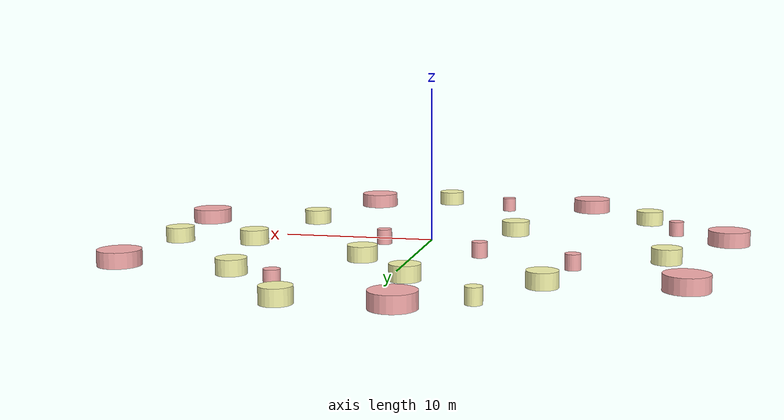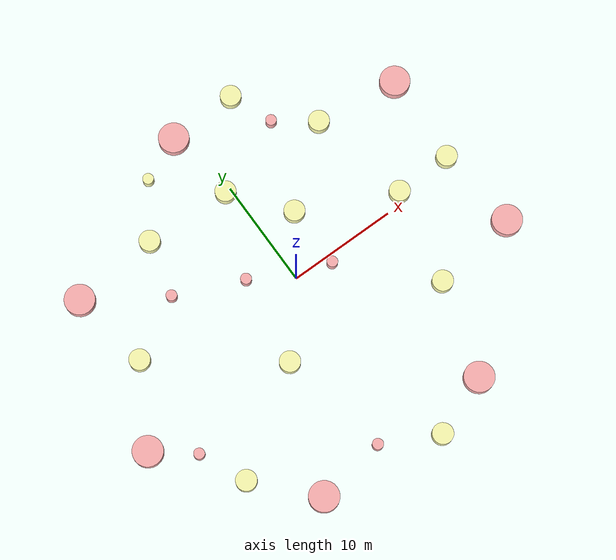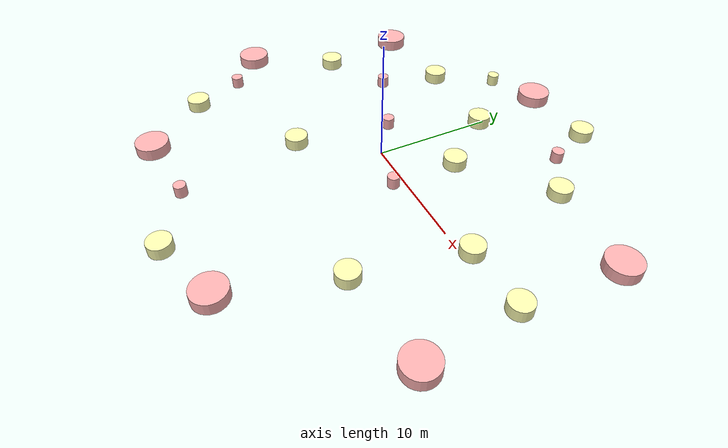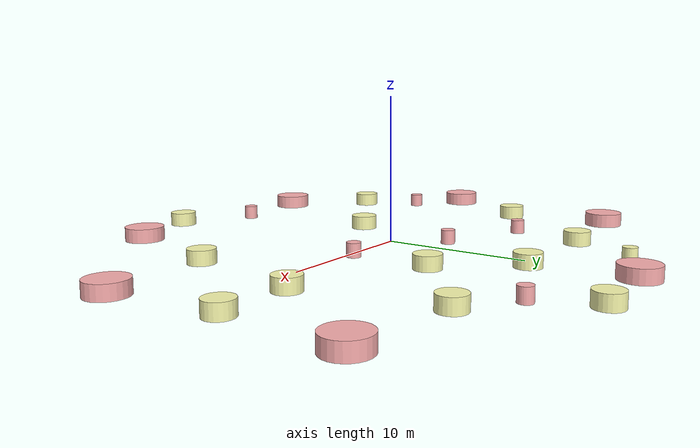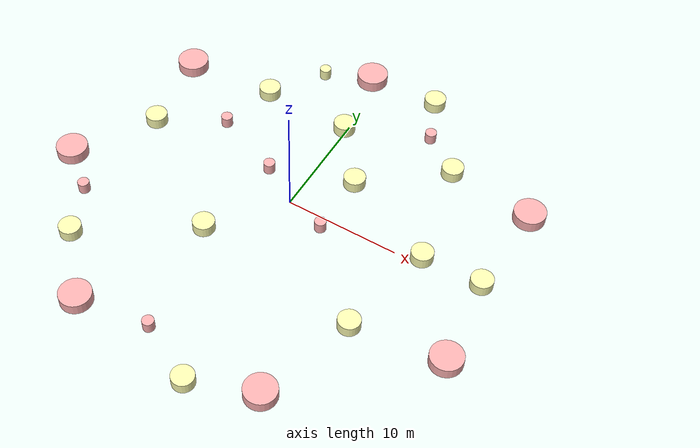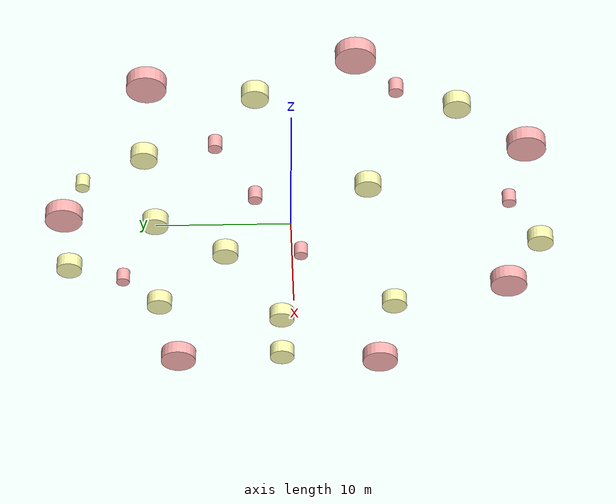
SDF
<?xml version='1.0'?>
<sdf version='1.6'>
  <model name='LandmarksColoured'>
    <link name='link_4'>
      <pose frame=''>-2.89321 -15.9613 0 0 -0 0</pose>
      <inertial>
        <mass>1</mass>
        <inertia>
          <ixx>0.145833</ixx>
          <ixy>0</ixy>
          <ixz>0</ixz>
          <iyy>0.145833</iyy>
          <iyz>0</iyz>
          <izz>0.125</izz>
        </inertia>
        <pose frame=''>0 0 0 0 -0 0</pose>
      </inertial>
      <self_collide>0</self_collide>
      <kinematic>0</kinematic>
      <visual name='visual'>
        <pose frame=''>0 0 0 0 -0 0</pose>
        <geometry>
          <cylinder>
            <radius>0.5</radius>
            <length>1</length>
          </cylinder>
        </geometry>
        <material>
          <lighting>1</lighting>
          <script>
            <uri>file://media/materials/scripts/gazebo.material</uri>
            <name>Gazebo/Grey</name>
          </script>
          <ambient>1 0.3 0.3 1</ambient>
          <diffuse>1 0.7 0.7 1</diffuse>
          <specular>1 0.01 0.01 1</specular>
          <emissive>1 0 0 1</emissive>
          <shader type='vertex'>
            <normal_map>__default__</normal_map>
          </shader>
        </material>
        <cast_shadows>1</cast_shadows>
        <transparency>0</transparency>
      </visual>
      <collision name='collision'>
        <laser_retro>0</laser_retro>
        <max_contacts>10</max_contacts>
        <pose frame=''>0 0 0 0 -0 0</pose>
        <geometry>
          <cylinder>
            <radius>0.5</radius>
            <length>1</length>
          </cylinder>
        </geometry>
        <surface>
          <friction>
            <ode>
              <mu>1</mu>
              <mu2>1</mu2>
              <fdir1>0 0 0</fdir1>
              <slip1>0</slip1>
              <slip2>0</slip2>
            </ode>
            <torsional>
              <coefficient>1</coefficient>
              <patch_radius>0</patch_radius>
              <surface_radius>0</surface_radius>
              <use_patch_radius>1</use_patch_radius>
              <ode>
                <slip>0</slip>
              </ode>
            </torsional>
          </friction>
          <bounce>
            <restitution_coefficient>0</restitution_coefficient>
            <threshold>1e+06</threshold>
          </bounce>
          <contact>
            <collide_without_contact>0</collide_without_contact>
            <collide_without_contact_bitmask>1</collide_without_contact_bitmask>
            <collide_bitmask>1</collide_bitmask>
            <ode>
              <soft_cfm>0</soft_cfm>
              <soft_erp>0.2</soft_erp>
              <kp>1e+13</kp>
              <kd>1</kd>
              <max_vel>0.01</max_vel>
              <min_depth>0</min_depth>
            </ode>
            <bullet>
              <split_impulse>1</split_impulse>
              <split_impulse_penetration_threshold>-0.01</split_impulse_penetration_threshold>
              <soft_cfm>0</soft_cfm>
              <soft_erp>0.2</soft_erp>
              <kp>1e+13</kp>
              <kd>1</kd>
            </bullet>
          </contact>
        </surface>
      </collision>
    </link>
    <link name='link_4_clone'>
      <pose frame=''>-5.38997 14.9192 -0 0 -0 0</pose>
      <inertial>
        <mass>1</mass>
        <inertia>
          <ixx>0.145833</ixx>
          <ixy>0</ixy>
          <ixz>0</ixz>
          <iyy>0.145833</iyy>
          <iyz>0</iyz>
          <izz>0.125</izz>
        </inertia>
        <pose frame=''>0 0 0 0 -0 0</pose>
      </inertial>
      <self_collide>0</self_collide>
      <kinematic>0</kinematic>
      <visual name='ModelPreview_4::link_4_clone::visual_1'>
        <pose frame=''>0 0 0 0 -0 0</pose>
        <geometry>
          <cylinder>
            <radius>0.5</radius>
            <length>1</length>
          </cylinder>
        </geometry>
        <material>
          <lighting>1</lighting>
          <script>
            <uri>file://media/materials/scripts/gazebo.material</uri>
            <name>Gazebo/Grey</name>
          </script>
          <ambient>1 1 0.3 1</ambient>
          <diffuse>1 1 0.7 1</diffuse>
          <specular>1 1 0.01 1</specular>
          <emissive>1 0 0 1</emissive>
          <shader type='vertex'>
            <normal_map>__default__</normal_map>
          </shader>
        </material>
        <cast_shadows>1</cast_shadows>
        <transparency>0</transparency>
      </visual>
      <visual name='visual'>
        <pose frame=''>0 0 0 0 -0 0</pose>
        <geometry>
          <cylinder>
            <radius>0.5</radius>
            <length>1</length>
          </cylinder>
        </geometry>
        <material>
          <lighting>1</lighting>
          <script>
            <uri>file://media/materials/scripts/gazebo.material</uri>
            <name>Gazebo/Grey</name>
          </script>
          <ambient>1 1 0.3 1</ambient>
          <diffuse>1 1 0.7 1</diffuse>
          <specular>1 1 0.01 1</specular>
          <emissive>1 1 0 1</emissive>
          <shader type='vertex'>
            <normal_map>__default__</normal_map>
          </shader>
        </material>
        <cast_shadows>1</cast_shadows>
        <transparency>0</transparency>
      </visual>
      <collision name='collision'>
        <laser_retro>0</laser_retro>
        <max_contacts>10</max_contacts>
        <pose frame=''>0 0 0 0 -0 0</pose>
        <geometry>
          <cylinder>
            <radius>0.5</radius>
            <length>1</length>
          </cylinder>
        </geometry>
        <surface>
          <friction>
            <ode>
              <mu>1</mu>
              <mu2>1</mu2>
              <fdir1>0 0 0</fdir1>
              <slip1>0</slip1>
              <slip2>0</slip2>
            </ode>
            <torsional>
              <coefficient>1</coefficient>
              <patch_radius>0</patch_radius>
              <surface_radius>0</surface_radius>
              <use_patch_radius>1</use_patch_radius>
              <ode>
                <slip>0</slip>
              </ode>
            </torsional>
          </friction>
          <bounce>
            <restitution_coefficient>0</restitution_coefficient>
            <threshold>1e+06</threshold>
          </bounce>
          <contact>
            <collide_without_contact>0</collide_without_contact>
            <collide_without_contact_bitmask>1</collide_without_contact_bitmask>
            <collide_bitmask>1</collide_bitmask>
            <ode>
              <soft_cfm>0</soft_cfm>
              <soft_erp>0.2</soft_erp>
              <kp>1e+13</kp>
              <kd>1</kd>
              <max_vel>0.01</max_vel>
              <min_depth>0</min_depth>
            </ode>
            <bullet>
              <split_impulse>1</split_impulse>
              <split_impulse_penetration_threshold>-0.01</split_impulse_penetration_threshold>
              <soft_cfm>0</soft_cfm>
              <soft_erp>0.2</soft_erp>
              <kp>1e+13</kp>
              <kd>1</kd>
            </bullet>
          </contact>
        </surface>
      </collision>
    </link>
    <link name='link_4_clone_0'>
      <pose frame=''>-16.491 9.53201 -0 0 -0 0</pose>
      <inertial>
        <mass>7.6137</mass>
        <inertia>
          <ixx>4.2575</ixx>
          <ixy>0</ixy>
          <ixz>0</ixz>
          <iyy>4.2575</iyy>
          <iyz>0</iyz>
          <izz>7.24605</izz>
        </inertia>
        <pose frame=''>0 0 0 0 -0 0</pose>
      </inertial>
      <self_collide>0</self_collide>
      <kinematic>0</kinematic>
      <visual name='visual'>
        <pose frame=''>0 0 0 0 -0 0</pose>
        <geometry>
          <cylinder>
            <radius>1.37965</radius>
            <length>1</length>
          </cylinder>
        </geometry>
        <material>
          <lighting>1</lighting>
          <script>
            <uri>file://media/materials/scripts/gazebo.material</uri>
            <name>Gazebo/Grey</name>
          </script>
          <ambient>1 0.3 0.3 1</ambient>
          <diffuse>1 0.7 0.7 1</diffuse>
          <specular>1 0.01 0.01 1</specular>
          <emissive>1 0 0 1</emissive>
          <shader type='vertex'>
            <normal_map>__default__</normal_map>
          </shader>
        </material>
        <cast_shadows>1</cast_shadows>
        <transparency>0</transparency>
      </visual>
      <collision name='collision'>
        <laser_retro>0</laser_retro>
        <max_contacts>10</max_contacts>
        <pose frame=''>0 0 0 0 -0 0</pose>
        <geometry>
          <cylinder>
            <radius>1.37965</radius>
            <length>1</length>
          </cylinder>
        </geometry>
        <surface>
          <friction>
            <ode>
              <mu>1</mu>
              <mu2>1</mu2>
              <fdir1>0 0 0</fdir1>
              <slip1>0</slip1>
              <slip2>0</slip2>
            </ode>
            <torsional>
              <coefficient>1</coefficient>
              <patch_radius>0</patch_radius>
              <surface_radius>0</surface_radius>
              <use_patch_radius>1</use_patch_radius>
              <ode>
                <slip>0</slip>
              </ode>
            </torsional>
          </friction>
          <bounce>
            <restitution_coefficient>0</restitution_coefficient>
            <threshold>1e+06</threshold>
          </bounce>
          <contact>
            <collide_without_contact>0</collide_without_contact>
            <collide_without_contact_bitmask>1</collide_without_contact_bitmask>
            <collide_bitmask>1</collide_bitmask>
            <ode>
              <soft_cfm>0</soft_cfm>
              <soft_erp>0.2</soft_erp>
              <kp>1e+13</kp>
              <kd>1</kd>
              <max_vel>0.01</max_vel>
              <min_depth>0</min_depth>
            </ode>
            <bullet>
              <split_impulse>1</split_impulse>
              <split_impulse_penetration_threshold>-0.01</split_impulse_penetration_threshold>
              <soft_cfm>0</soft_cfm>
              <soft_erp>0.2</soft_erp>
              <kp>1e+13</kp>
              <kd>1</kd>
            </bullet>
          </contact>
        </surface>
      </collision>
    </link>
    <link name='link_4_clone_0_clone'>
      <pose frame=''>-19.3072 -4.8348 -0 0 -0 0</pose>
      <inertial>
        <mass>7.6137</mass>
        <inertia>
          <ixx>4.2575</ixx>
          <ixy>0</ixy>
          <ixz>0</ixz>
          <iyy>4.2575</iyy>
          <iyz>0</iyz>
          <izz>7.24605</izz>
        </inertia>
        <pose frame=''>0 0 0 0 -0 0</pose>
      </inertial>
      <self_collide>0</self_collide>
      <kinematic>0</kinematic>
      <visual name='visual'>
        <pose frame=''>0 0 0 0 -0 0</pose>
        <geometry>
          <cylinder>
            <radius>1.37965</radius>
            <length>1</length>
          </cylinder>
        </geometry>
        <material>
          <lighting>1</lighting>
          <script>
            <uri>file://media/materials/scripts/gazebo.material</uri>
            <name>Gazebo/Grey</name>
          </script>
          <ambient>1 0.3 0.3 1</ambient>
          <diffuse>1 0.7 0.7 1</diffuse>
          <specular>1 0.01 0.01 1</specular>
          <emissive>1 0 0 1</emissive>
          <shader type='vertex'>
            <normal_map>__default__</normal_map>
          </shader>
        </material>
        <cast_shadows>1</cast_shadows>
        <transparency>0</transparency>
      </visual>
      <collision name='collision'>
        <laser_retro>0</laser_retro>
        <max_contacts>10</max_contacts>
        <pose frame=''>0 0 0 0 -0 0</pose>
        <geometry>
          <cylinder>
            <radius>1.37965</radius>
            <length>1</length>
          </cylinder>
        </geometry>
        <surface>
          <friction>
            <ode>
              <mu>1</mu>
              <mu2>1</mu2>
              <fdir1>0 0 0</fdir1>
              <slip1>0</slip1>
              <slip2>0</slip2>
            </ode>
            <torsional>
              <coefficient>1</coefficient>
              <patch_radius>0</patch_radius>
              <surface_radius>0</surface_radius>
              <use_patch_radius>1</use_patch_radius>
              <ode>
                <slip>0</slip>
              </ode>
            </torsional>
          </friction>
          <bounce>
            <restitution_coefficient>0</restitution_coefficient>
            <threshold>1e+06</threshold>
          </bounce>
          <contact>
            <collide_without_contact>0</collide_without_contact>
            <collide_without_contact_bitmask>1</collide_without_contact_bitmask>
            <collide_bitmask>1</collide_bitmask>
            <ode>
              <soft_cfm>0</soft_cfm>
              <soft_erp>0.2</soft_erp>
              <kp>1e+13</kp>
              <kd>1</kd>
              <max_vel>0.01</max_vel>
              <min_depth>0</min_depth>
            </ode>
            <bullet>
              <split_impulse>1</split_impulse>
              <split_impulse_penetration_threshold>-0.01</split_impulse_penetration_threshold>
              <soft_cfm>0</soft_cfm>
              <soft_erp>0.2</soft_erp>
              <kp>1e+13</kp>
              <kd>1</kd>
            </bullet>
          </contact>
        </surface>
      </collision>
    </link>
    <link name='link_4_clone_0_clone_0'>
      <pose frame=''>18.101 -6.65934 0 0 -0 0</pose>
      <inertial>
        <mass>7.6137</mass>
        <inertia>
          <ixx>4.2575</ixx>
          <ixy>0</ixy>
          <ixz>0</ixz>
          <iyy>4.2575</iyy>
          <iyz>0</iyz>
          <izz>7.24605</izz>
        </inertia>
        <pose frame=''>0 0 0 0 -0 0</pose>
      </inertial>
      <self_collide>0</self_collide>
      <kinematic>0</kinematic>
      <visual name='visual'>
        <pose frame=''>0 0 0 0 -0 0</pose>
        <geometry>
          <cylinder>
            <radius>1.37965</radius>
            <length>1</length>
          </cylinder>
        </geometry>
        <material>
          <lighting>1</lighting>
          <script>
            <uri>file://media/materials/scripts/gazebo.material</uri>
            <name>Gazebo/Grey</name>
          </script>
          <ambient>1 0.3 0.3 1</ambient>
          <diffuse>1 0.7 0.7 1</diffuse>
          <specular>1 0.01 0.01 1</specular>
          <emissive>1 0 0 1</emissive>
          <shader type='vertex'>
            <normal_map>__default__</normal_map>
          </shader>
        </material>
        <cast_shadows>1</cast_shadows>
        <transparency>0</transparency>
      </visual>
      <collision name='collision'>
        <laser_retro>0</laser_retro>
        <max_contacts>10</max_contacts>
        <pose frame=''>0 0 0 0 -0 0</pose>
        <geometry>
          <cylinder>
            <radius>1.37965</radius>
            <length>1</length>
          </cylinder>
        </geometry>
        <surface>
          <friction>
            <ode>
              <mu>1</mu>
              <mu2>1</mu2>
              <fdir1>0 0 0</fdir1>
              <slip1>0</slip1>
              <slip2>0</slip2>
            </ode>
            <torsional>
              <coefficient>1</coefficient>
              <patch_radius>0</patch_radius>
              <surface_radius>0</surface_radius>
              <use_patch_radius>1</use_patch_radius>
              <ode>
                <slip>0</slip>
              </ode>
            </torsional>
          </friction>
          <bounce>
            <restitution_coefficient>0</restitution_coefficient>
            <threshold>1e+06</threshold>
          </bounce>
          <contact>
            <collide_without_contact>0</collide_without_contact>
            <collide_without_contact_bitmask>1</collide_without_contact_bitmask>
            <collide_bitmask>1</collide_bitmask>
            <ode>
              <soft_cfm>0</soft_cfm>
              <soft_erp>0.2</soft_erp>
              <kp>1e+13</kp>
              <kd>1</kd>
              <max_vel>0.01</max_vel>
              <min_depth>0</min_depth>
            </ode>
            <bullet>
              <split_impulse>1</split_impulse>
              <split_impulse_penetration_threshold>-0.01</split_impulse_penetration_threshold>
              <soft_cfm>0</soft_cfm>
              <soft_erp>0.2</soft_erp>
              <kp>1e+13</kp>
              <kd>1</kd>
            </bullet>
          </contact>
        </surface>
      </collision>
    </link>
    <link name='link_4_clone_0_clone_1'>
      <pose frame=''>17.6574 9.38126 0 0 -0 0</pose>
      <inertial>
        <mass>7.6137</mass>
        <inertia>
          <ixx>4.2575</ixx>
          <ixy>0</ixy>
          <ixz>0</ixz>
          <iyy>4.2575</iyy>
          <iyz>0</iyz>
          <izz>7.24605</izz>
        </inertia>
        <pose frame=''>0 0 0 0 -0 0</pose>
      </inertial>
      <self_collide>0</self_collide>
      <kinematic>0</kinematic>
      <visual name='visual'>
        <pose frame=''>0 0 0 0 -0 0</pose>
        <geometry>
          <cylinder>
            <radius>1.37965</radius>
            <length>1</length>
          </cylinder>
        </geometry>
        <material>
          <lighting>1</lighting>
          <script>
            <uri>file://media/materials/scripts/gazebo.material</uri>
            <name>Gazebo/Grey</name>
          </script>
          <ambient>1 0.3 0.3 1</ambient>
          <diffuse>1 0.7 0.7 1</diffuse>
          <specular>1 0.01 0.01 1</specular>
          <emissive>1 0 0 1</emissive>
          <shader type='vertex'>
            <normal_map>__default__</normal_map>
          </shader>
        </material>
        <cast_shadows>1</cast_shadows>
        <transparency>0</transparency>
      </visual>
      <collision name='collision'>
        <laser_retro>0</laser_retro>
        <max_contacts>10</max_contacts>
        <pose frame=''>0 0 0 0 -0 0</pose>
        <geometry>
          <cylinder>
            <radius>1.37965</radius>
            <length>1</length>
          </cylinder>
        </geometry>
        <surface>
          <friction>
            <ode>
              <mu>1</mu>
              <mu2>1</mu2>
              <fdir1>0 0 0</fdir1>
              <slip1>0</slip1>
              <slip2>0</slip2>
            </ode>
            <torsional>
              <coefficient>1</coefficient>
              <patch_radius>0</patch_radius>
              <surface_radius>0</surface_radius>
              <use_patch_radius>1</use_patch_radius>
              <ode>
                <slip>0</slip>
              </ode>
            </torsional>
          </friction>
          <bounce>
            <restitution_coefficient>0</restitution_coefficient>
            <threshold>1e+06</threshold>
          </bounce>
          <contact>
            <collide_without_contact>0</collide_without_contact>
            <collide_without_contact_bitmask>1</collide_without_contact_bitmask>
            <collide_bitmask>1</collide_bitmask>
            <ode>
              <soft_cfm>0</soft_cfm>
              <soft_erp>0.2</soft_erp>
              <kp>1e+13</kp>
              <kd>1</kd>
              <max_vel>0.01</max_vel>
              <min_depth>0</min_depth>
            </ode>
            <bullet>
              <split_impulse>1</split_impulse>
              <split_impulse_penetration_threshold>-0.01</split_impulse_penetration_threshold>
              <soft_cfm>0</soft_cfm>
              <soft_erp>0.2</soft_erp>
              <kp>1e+13</kp>
              <kd>1</kd>
            </bullet>
          </contact>
        </surface>
      </collision>
    </link>
    <link name='link_4_clone_0_clone_2'>
      <pose frame=''>-1.39165 16.6645 -0 0 -0 0</pose>
      <inertial>
        <mass>7.6137</mass>
        <inertia>
          <ixx>4.2575</ixx>
          <ixy>0</ixy>
          <ixz>0</ixz>
          <iyy>4.2575</iyy>
          <iyz>0</iyz>
          <izz>7.24605</izz>
        </inertia>
        <pose frame=''>0 0 0 0 -0 0</pose>
      </inertial>
      <self_collide>0</self_collide>
      <kinematic>0</kinematic>
      <visual name='visual'>
        <pose frame=''>0 0 0 0 -0 0</pose>
        <geometry>
          <cylinder>
            <radius>1.37965</radius>
            <length>1</length>
          </cylinder>
        </geometry>
        <material>
          <lighting>1</lighting>
          <script>
            <uri>file://media/materials/scripts/gazebo.material</uri>
            <name>Gazebo/Grey</name>
          </script>
          <ambient>1 0.3 0.3 1</ambient>
          <diffuse>1 0.7 0.7 1</diffuse>
          <specular>1 0.01 0.01 1</specular>
          <emissive>1 0 0 1</emissive>
          <shader type='vertex'>
            <normal_map>__default__</normal_map>
          </shader>
        </material>
        <cast_shadows>1</cast_shadows>
        <transparency>0</transparency>
      </visual>
      <collision name='collision'>
        <laser_retro>0</laser_retro>
        <max_contacts>10</max_contacts>
        <pose frame=''>0 0 0 0 -0 0</pose>
        <geometry>
          <cylinder>
            <radius>1.37965</radius>
            <length>1</length>
          </cylinder>
        </geometry>
        <surface>
          <friction>
            <ode>
              <mu>1</mu>
              <mu2>1</mu2>
              <fdir1>0 0 0</fdir1>
              <slip1>0</slip1>
              <slip2>0</slip2>
            </ode>
            <torsional>
              <coefficient>1</coefficient>
              <patch_radius>0</patch_radius>
              <surface_radius>0</surface_radius>
              <use_patch_radius>1</use_patch_radius>
              <ode>
                <slip>0</slip>
              </ode>
            </torsional>
          </friction>
          <bounce>
            <restitution_coefficient>0</restitution_coefficient>
            <threshold>1e+06</threshold>
          </bounce>
          <contact>
            <collide_without_contact>0</collide_without_contact>
            <collide_without_contact_bitmask>1</collide_without_contact_bitmask>
            <collide_bitmask>1</collide_bitmask>
            <ode>
              <soft_cfm>0</soft_cfm>
              <soft_erp>0.2</soft_erp>
              <kp>1e+13</kp>
              <kd>1</kd>
              <max_vel>0.01</max_vel>
              <min_depth>0</min_depth>
            </ode>
            <bullet>
              <split_impulse>1</split_impulse>
              <split_impulse_penetration_threshold>-0.01</split_impulse_penetration_threshold>
              <soft_cfm>0</soft_cfm>
              <soft_erp>0.2</soft_erp>
              <kp>1e+13</kp>
              <kd>1</kd>
            </bullet>
          </contact>
        </surface>
      </collision>
    </link>
    <link name='link_4_clone_0_clone_clone'>
      <pose frame=''>-9.29686 -16.885 0 0 -0 0</pose>
      <inertial>
        <mass>7.6137</mass>
        <inertia>
          <ixx>4.2575</ixx>
          <ixy>0</ixy>
          <ixz>0</ixz>
          <iyy>4.2575</iyy>
          <iyz>0</iyz>
          <izz>7.24605</izz>
        </inertia>
        <pose frame=''>0 0 0 0 -0 0</pose>
      </inertial>
      <self_collide>0</self_collide>
      <kinematic>0</kinematic>
      <visual name='visual'>
        <pose frame=''>0 0 0 0 -0 0</pose>
        <geometry>
          <cylinder>
            <radius>1.37965</radius>
            <length>1</length>
          </cylinder>
        </geometry>
        <material>
          <lighting>1</lighting>
          <script>
            <uri>file://media/materials/scripts/gazebo.material</uri>
            <name>Gazebo/Grey</name>
          </script>
          <ambient>1 0.3 0.3 1</ambient>
          <diffuse>1 0.7 0.7 1</diffuse>
          <specular>1 0.01 0.01 1</specular>
          <emissive>1 0 0 1</emissive>
          <shader type='vertex'>
            <normal_map>__default__</normal_map>
          </shader>
        </material>
        <cast_shadows>1</cast_shadows>
        <transparency>0</transparency>
      </visual>
      <collision name='collision'>
        <laser_retro>0</laser_retro>
        <max_contacts>10</max_contacts>
        <pose frame=''>0 0 0 0 -0 0</pose>
        <geometry>
          <cylinder>
            <radius>1.37965</radius>
            <length>1</length>
          </cylinder>
        </geometry>
        <surface>
          <friction>
            <ode>
              <mu>1</mu>
              <mu2>1</mu2>
              <fdir1>0 0 0</fdir1>
              <slip1>0</slip1>
              <slip2>0</slip2>
            </ode>
            <torsional>
              <coefficient>1</coefficient>
              <patch_radius>0</patch_radius>
              <surface_radius>0</surface_radius>
              <use_patch_radius>1</use_patch_radius>
              <ode>
                <slip>0</slip>
              </ode>
            </torsional>
          </friction>
          <bounce>
            <restitution_coefficient>0</restitution_coefficient>
            <threshold>1e+06</threshold>
          </bounce>
          <contact>
            <collide_without_contact>0</collide_without_contact>
            <collide_without_contact_bitmask>1</collide_without_contact_bitmask>
            <collide_bitmask>1</collide_bitmask>
            <ode>
              <soft_cfm>0</soft_cfm>
              <soft_erp>0.2</soft_erp>
              <kp>1e+13</kp>
              <kd>1</kd>
              <max_vel>0.01</max_vel>
              <min_depth>0</min_depth>
            </ode>
            <bullet>
              <split_impulse>1</split_impulse>
              <split_impulse_penetration_threshold>-0.01</split_impulse_penetration_threshold>
              <soft_cfm>0</soft_cfm>
              <soft_erp>0.2</soft_erp>
              <kp>1e+13</kp>
              <kd>1</kd>
            </bullet>
          </contact>
        </surface>
      </collision>
    </link>
    <link name='link_4_clone_0_clone_clone_0'>
      <pose frame=''>7.70314 -16.4099 0 0 -0 0</pose>
      <inertial>
        <mass>7.6137</mass>
        <inertia>
          <ixx>4.2575</ixx>
          <ixy>0</ixy>
          <ixz>0</ixz>
          <iyy>4.2575</iyy>
          <iyz>0</iyz>
          <izz>7.24605</izz>
        </inertia>
        <pose frame=''>0 0 0 0 -0 0</pose>
      </inertial>
      <self_collide>0</self_collide>
      <kinematic>0</kinematic>
      <visual name='visual'>
        <pose frame=''>0 0 0 0 -0 0</pose>
        <geometry>
          <cylinder>
            <radius>1.37965</radius>
            <length>1</length>
          </cylinder>
        </geometry>
        <material>
          <lighting>1</lighting>
          <script>
            <uri>file://media/materials/scripts/gazebo.material</uri>
            <name>Gazebo/Grey</name>
          </script>
          <ambient>1 0.3 0.3 1</ambient>
          <diffuse>1 0.7 0.7 1</diffuse>
          <specular>1 0.01 0.01 1</specular>
          <emissive>1 0 0 1</emissive>
          <shader type='vertex'>
            <normal_map>__default__</normal_map>
          </shader>
        </material>
        <cast_shadows>1</cast_shadows>
        <transparency>0</transparency>
      </visual>
      <collision name='collision'>
        <laser_retro>0</laser_retro>
        <max_contacts>10</max_contacts>
        <pose frame=''>0 0 0 0 -0 0</pose>
        <geometry>
          <cylinder>
            <radius>1.37965</radius>
            <length>1</length>
          </cylinder>
        </geometry>
        <surface>
          <friction>
            <ode>
              <mu>1</mu>
              <mu2>1</mu2>
              <fdir1>0 0 0</fdir1>
              <slip1>0</slip1>
              <slip2>0</slip2>
            </ode>
            <torsional>
              <coefficient>1</coefficient>
              <patch_radius>0</patch_radius>
              <surface_radius>0</surface_radius>
              <use_patch_radius>1</use_patch_radius>
              <ode>
                <slip>0</slip>
              </ode>
            </torsional>
          </friction>
          <bounce>
            <restitution_coefficient>0</restitution_coefficient>
            <threshold>1e+06</threshold>
          </bounce>
          <contact>
            <collide_without_contact>0</collide_without_contact>
            <collide_without_contact_bitmask>1</collide_without_contact_bitmask>
            <collide_bitmask>1</collide_bitmask>
            <ode>
              <soft_cfm>0</soft_cfm>
              <soft_erp>0.2</soft_erp>
              <kp>1e+13</kp>
              <kd>1</kd>
              <max_vel>0.01</max_vel>
              <min_depth>0</min_depth>
            </ode>
            <bullet>
              <split_impulse>1</split_impulse>
              <split_impulse_penetration_threshold>-0.01</split_impulse_penetration_threshold>
              <soft_cfm>0</soft_cfm>
              <soft_erp>0.2</soft_erp>
              <kp>1e+13</kp>
              <kd>1</kd>
            </bullet>
          </contact>
        </surface>
      </collision>
    </link>
    <link name='link_4_clone_1'>
      <pose frame=''>-15.8394 -7.60505 1.4e-05 0 -0 0</pose>
      <inertial>
        <mass>1</mass>
        <inertia>
          <ixx>0.145833</ixx>
          <ixy>0</ixy>
          <ixz>0</ixz>
          <iyy>0.145833</iyy>
          <iyz>0</iyz>
          <izz>0.125</izz>
        </inertia>
        <pose frame=''>0 0 0 0 -0 0</pose>
      </inertial>
      <self_collide>0</self_collide>
      <kinematic>0</kinematic>
      <visual name='visual'>
        <pose frame=''>0 0 0 0 -0 0</pose>
        <geometry>
          <cylinder>
            <radius>0.5</radius>
            <length>1</length>
          </cylinder>
        </geometry>
        <material>
          <lighting>1</lighting>
          <script>
            <uri>file://media/materials/scripts/gazebo.material</uri>
            <name>Gazebo/Grey</name>
          </script>
          <ambient>1 0.3 0.3 1</ambient>
          <diffuse>1 0.7 0.7 1</diffuse>
          <specular>1 0.01 0.01 1</specular>
          <emissive>1 0 0 1</emissive>
          <shader type='vertex'>
            <normal_map>__default__</normal_map>
          </shader>
        </material>
        <cast_shadows>1</cast_shadows>
        <transparency>0</transparency>
      </visual>
      <collision name='collision'>
        <laser_retro>0</laser_retro>
        <max_contacts>10</max_contacts>
        <pose frame=''>0 0 0 0 -0 0</pose>
        <geometry>
          <cylinder>
            <radius>0.5</radius>
            <length>1</length>
          </cylinder>
        </geometry>
        <surface>
          <friction>
            <ode>
              <mu>1</mu>
              <mu2>1</mu2>
              <fdir1>0 0 0</fdir1>
              <slip1>0</slip1>
              <slip2>0</slip2>
            </ode>
            <torsional>
              <coefficient>1</coefficient>
              <patch_radius>0</patch_radius>
              <surface_radius>0</surface_radius>
              <use_patch_radius>1</use_patch_radius>
              <ode>
                <slip>0</slip>
              </ode>
            </torsional>
          </friction>
          <bounce>
            <restitution_coefficient>0</restitution_coefficient>
            <threshold>1e+06</threshold>
          </bounce>
          <contact>
            <collide_without_contact>0</collide_without_contact>
            <collide_without_contact_bitmask>1</collide_without_contact_bitmask>
            <collide_bitmask>1</collide_bitmask>
            <ode>
              <soft_cfm>0</soft_cfm>
              <soft_erp>0.2</soft_erp>
              <kp>1e+13</kp>
              <kd>1</kd>
              <max_vel>0.01</max_vel>
              <min_depth>0</min_depth>
            </ode>
            <bullet>
              <split_impulse>1</split_impulse>
              <split_impulse_penetration_threshold>-0.01</split_impulse_penetration_threshold>
              <soft_cfm>0</soft_cfm>
              <soft_erp>0.2</soft_erp>
              <kp>1e+13</kp>
              <kd>1</kd>
            </bullet>
          </contact>
        </surface>
      </collision>
    </link>
    <link name='link_4_clone_2'>
      <pose frame=''>3.40156 -0.6744 1e-05 0 -0 0</pose>
      <inertial>
        <mass>1</mass>
        <inertia>
          <ixx>0.145833</ixx>
          <ixy>0</ixy>
          <ixz>0</ixz>
          <iyy>0.145833</iyy>
          <iyz>0</iyz>
          <izz>0.125</izz>
        </inertia>
        <pose frame=''>0 0 0 0 -0 0</pose>
      </inertial>
      <self_collide>0</self_collide>
      <kinematic>0</kinematic>
      <visual name='visual'>
        <pose frame=''>0 0 0 0 -0 0</pose>
        <geometry>
          <cylinder>
            <radius>0.5</radius>
            <length>1</length>
          </cylinder>
        </geometry>
        <material>
          <lighting>1</lighting>
          <script>
            <uri>file://media/materials/scripts/gazebo.material</uri>
            <name>Gazebo/Grey</name>
          </script>
          <ambient>1 0.3 0.3 1</ambient>
          <diffuse>1 0.7 0.7 1</diffuse>
          <specular>1 0.01 0.01 1</specular>
          <emissive>1 0 0 1</emissive>
          <shader type='vertex'>
            <normal_map>__default__</normal_map>
          </shader>
        </material>
        <cast_shadows>1</cast_shadows>
        <transparency>0</transparency>
      </visual>
      <collision name='collision'>
        <laser_retro>0</laser_retro>
        <max_contacts>10</max_contacts>
        <pose frame=''>0 0 0 0 -0 0</pose>
        <geometry>
          <cylinder>
            <radius>0.5</radius>
            <length>1</length>
          </cylinder>
        </geometry>
        <surface>
          <friction>
            <ode>
              <mu>1</mu>
              <mu2>1</mu2>
              <fdir1>0 0 0</fdir1>
              <slip1>0</slip1>
              <slip2>0</slip2>
            </ode>
            <torsional>
              <coefficient>1</coefficient>
              <patch_radius>0</patch_radius>
              <surface_radius>0</surface_radius>
              <use_patch_radius>1</use_patch_radius>
              <ode>
                <slip>0</slip>
              </ode>
            </torsional>
          </friction>
          <bounce>
            <restitution_coefficient>0</restitution_coefficient>
            <threshold>1e+06</threshold>
          </bounce>
          <contact>
            <collide_without_contact>0</collide_without_contact>
            <collide_without_contact_bitmask>1</collide_without_contact_bitmask>
            <collide_bitmask>1</collide_bitmask>
            <ode>
              <soft_cfm>0</soft_cfm>
              <soft_erp>0.2</soft_erp>
              <kp>1e+13</kp>
              <kd>1</kd>
              <max_vel>0.01</max_vel>
              <min_depth>0</min_depth>
            </ode>
            <bullet>
              <split_impulse>1</split_impulse>
              <split_impulse_penetration_threshold>-0.01</split_impulse_penetration_threshold>
              <soft_cfm>0</soft_cfm>
              <soft_erp>0.2</soft_erp>
              <kp>1e+13</kp>
              <kd>1</kd>
            </bullet>
          </contact>
        </surface>
      </collision>
    </link>
    <link name='link_4_clone_3'>
      <pose frame=''>6.57429 12.9229 1.5e-05 0 -0 0</pose>
      <inertial>
        <mass>1</mass>
        <inertia>
          <ixx>0.145833</ixx>
          <ixy>0</ixy>
          <ixz>0</ixz>
          <iyy>0.145833</iyy>
          <iyz>0</iyz>
          <izz>0.125</izz>
        </inertia>
        <pose frame=''>0 0 0 0 -0 0</pose>
      </inertial>
      <self_collide>0</self_collide>
      <kinematic>0</kinematic>
      <visual name='visual'>
        <pose frame=''>0 0 0 0 -0 0</pose>
        <geometry>
          <cylinder>
            <radius>0.5</radius>
            <length>1</length>
          </cylinder>
        </geometry>
        <material>
          <lighting>1</lighting>
          <script>
            <uri>file://media/materials/scripts/gazebo.material</uri>
            <name>Gazebo/Grey</name>
          </script>
          <ambient>1 0.3 0.3 1</ambient>
          <diffuse>1 0.7 0.7 1</diffuse>
          <specular>1 0.01 0.01 1</specular>
          <emissive>1 0 0 1</emissive>
          <shader type='vertex'>
            <normal_map>__default__</normal_map>
          </shader>
        </material>
        <cast_shadows>1</cast_shadows>
        <transparency>0</transparency>
      </visual>
      <collision name='collision'>
        <laser_retro>0</laser_retro>
        <max_contacts>10</max_contacts>
        <pose frame=''>0 0 0 0 -0 0</pose>
        <geometry>
          <cylinder>
            <radius>0.5</radius>
            <length>1</length>
          </cylinder>
        </geometry>
        <surface>
          <friction>
            <ode>
              <mu>1</mu>
              <mu2>1</mu2>
              <fdir1>0 0 0</fdir1>
              <slip1>0</slip1>
              <slip2>0</slip2>
            </ode>
            <torsional>
              <coefficient>1</coefficient>
              <patch_radius>0</patch_radius>
              <surface_radius>0</surface_radius>
              <use_patch_radius>1</use_patch_radius>
              <ode>
                <slip>0</slip>
              </ode>
            </torsional>
          </friction>
          <bounce>
            <restitution_coefficient>0</restitution_coefficient>
            <threshold>1e+06</threshold>
          </bounce>
          <contact>
            <collide_without_contact>0</collide_without_contact>
            <collide_without_contact_bitmask>1</collide_without_contact_bitmask>
            <collide_bitmask>1</collide_bitmask>
            <ode>
              <soft_cfm>0</soft_cfm>
              <soft_erp>0.2</soft_erp>
              <kp>1e+13</kp>
              <kd>1</kd>
              <max_vel>0.01</max_vel>
              <min_depth>0</min_depth>
            </ode>
            <bullet>
              <split_impulse>1</split_impulse>
              <split_impulse_penetration_threshold>-0.01</split_impulse_penetration_threshold>
              <soft_cfm>0</soft_cfm>
              <soft_erp>0.2</soft_erp>
              <kp>1e+13</kp>
              <kd>1</kd>
            </bullet>
          </contact>
        </surface>
      </collision>
    </link>
    <link name='link_4_clone_4'>
      <pose frame=''>-3.62741 2.51345 -8e-06 0 -0 0</pose>
      <inertial>
        <mass>1</mass>
        <inertia>
          <ixx>0.145833</ixx>
          <ixy>0</ixy>
          <ixz>0</ixz>
          <iyy>0.145833</iyy>
          <iyz>0</iyz>
          <izz>0.125</izz>
        </inertia>
        <pose frame=''>0 0 0 0 -0 0</pose>
      </inertial>
      <self_collide>0</self_collide>
      <kinematic>0</kinematic>
      <visual name='visual'>
        <pose frame=''>0 0 0 0 -0 0</pose>
        <geometry>
          <cylinder>
            <radius>0.5</radius>
            <length>1</length>
          </cylinder>
        </geometry>
        <material>
          <lighting>1</lighting>
          <script>
            <uri>file://media/materials/scripts/gazebo.material</uri>
            <name>Gazebo/Grey</name>
          </script>
          <ambient>1 0.3 0.3 1</ambient>
          <diffuse>1 0.7 0.7 1</diffuse>
          <specular>1 0.01 0.01 1</specular>
          <emissive>1 0 0 1</emissive>
          <shader type='vertex'>
            <normal_map>__default__</normal_map>
          </shader>
        </material>
        <cast_shadows>1</cast_shadows>
        <transparency>0</transparency>
      </visual>
      <collision name='collision'>
        <laser_retro>0</laser_retro>
        <max_contacts>10</max_contacts>
        <pose frame=''>0 0 0 0 -0 0</pose>
        <geometry>
          <cylinder>
            <radius>0.5</radius>
            <length>1</length>
          </cylinder>
        </geometry>
        <surface>
          <friction>
            <ode>
              <mu>1</mu>
              <mu2>1</mu2>
              <fdir1>0 0 0</fdir1>
              <slip1>0</slip1>
              <slip2>0</slip2>
            </ode>
            <torsional>
              <coefficient>1</coefficient>
              <patch_radius>0</patch_radius>
              <surface_radius>0</surface_radius>
              <use_patch_radius>1</use_patch_radius>
              <ode>
                <slip>0</slip>
              </ode>
            </torsional>
          </friction>
          <bounce>
            <restitution_coefficient>0</restitution_coefficient>
            <threshold>1e+06</threshold>
          </bounce>
          <contact>
            <collide_without_contact>0</collide_without_contact>
            <collide_without_contact_bitmask>1</collide_without_contact_bitmask>
            <collide_bitmask>1</collide_bitmask>
            <ode>
              <soft_cfm>0</soft_cfm>
              <soft_erp>0.2</soft_erp>
              <kp>1e+13</kp>
              <kd>1</kd>
              <max_vel>0.01</max_vel>
              <min_depth>0</min_depth>
            </ode>
            <bullet>
              <split_impulse>1</split_impulse>
              <split_impulse_penetration_threshold>-0.01</split_impulse_penetration_threshold>
              <soft_cfm>0</soft_cfm>
              <soft_erp>0.2</soft_erp>
              <kp>1e+13</kp>
              <kd>1</kd>
            </bullet>
          </contact>
        </surface>
      </collision>
    </link>
    <link name='link_4_clone_5'>
      <pose frame=''>-9.77094 5.13198 1.4e-05 0 -0 0</pose>
      <inertial>
        <mass>1</mass>
        <inertia>
          <ixx>0.145833</ixx>
          <ixy>0</ixy>
          <ixz>0</ixz>
          <iyy>0.145833</iyy>
          <iyz>0</iyz>
          <izz>0.125</izz>
        </inertia>
        <pose frame=''>0 0 0 0 -0 0</pose>
      </inertial>
      <self_collide>0</self_collide>
      <kinematic>0</kinematic>
      <visual name='visual'>
        <pose frame=''>0 0 0 0 -0 0</pose>
        <geometry>
          <cylinder>
            <radius>0.5</radius>
            <length>1</length>
          </cylinder>
        </geometry>
        <material>
          <lighting>1</lighting>
          <script>
            <uri>file://media/materials/scripts/gazebo.material</uri>
            <name>Gazebo/Grey</name>
          </script>
          <ambient>1 0.3 0.3 1</ambient>
          <diffuse>1 0.7 0.7 1</diffuse>
          <specular>1 0.01 0.01 1</specular>
          <emissive>1 0 0 1</emissive>
          <shader type='vertex'>
            <normal_map>__default__</normal_map>
          </shader>
        </material>
        <cast_shadows>1</cast_shadows>
        <transparency>0</transparency>
      </visual>
      <collision name='collision'>
        <laser_retro>0</laser_retro>
        <max_contacts>10</max_contacts>
        <pose frame=''>0 0 0 0 -0 0</pose>
        <geometry>
          <cylinder>
            <radius>0.5</radius>
            <length>1</length>
          </cylinder>
        </geometry>
        <surface>
          <friction>
            <ode>
              <mu>1</mu>
              <mu2>1</mu2>
              <fdir1>0 0 0</fdir1>
              <slip1>0</slip1>
              <slip2>0</slip2>
            </ode>
            <torsional>
              <coefficient>1</coefficient>
              <patch_radius>0</patch_radius>
              <surface_radius>0</surface_radius>
              <use_patch_radius>1</use_patch_radius>
              <ode>
                <slip>0</slip>
              </ode>
            </torsional>
          </friction>
          <bounce>
            <restitution_coefficient>0</restitution_coefficient>
            <threshold>1e+06</threshold>
          </bounce>
          <contact>
            <collide_without_contact>0</collide_without_contact>
            <collide_without_contact_bitmask>1</collide_without_contact_bitmask>
            <collide_bitmask>1</collide_bitmask>
            <ode>
              <soft_cfm>0</soft_cfm>
              <soft_erp>0.2</soft_erp>
              <kp>1e+13</kp>
              <kd>1</kd>
              <max_vel>0.01</max_vel>
              <min_depth>0</min_depth>
            </ode>
            <bullet>
              <split_impulse>1</split_impulse>
              <split_impulse_penetration_threshold>-0.01</split_impulse_penetration_threshold>
              <soft_cfm>0</soft_cfm>
              <soft_erp>0.2</soft_erp>
              <kp>1e+13</kp>
              <kd>1</kd>
            </bullet>
          </contact>
        </surface>
      </collision>
    </link>
    <link name='link_4_clone_clone'>
      <pose frame=''>10.2323 -7.72786 0 0 -0 0</pose>
      <inertial>
        <mass>3.64615</mass>
        <inertia>
          <ixx>1.13475</ixx>
          <ixy>0</ixy>
          <ixz>0</ixz>
          <iyy>1.13475</iyy>
          <iyz>0</iyz>
          <izz>1.6618</izz>
        </inertia>
        <pose frame=''>0 0 0 0 -0 0</pose>
      </inertial>
      <self_collide>0</self_collide>
      <kinematic>0</kinematic>
      <visual name='visual_1'>
        <pose frame=''>0 0 0 0 -0 0</pose>
        <geometry>
          <cylinder>
            <radius>0.954744</radius>
            <length>1</length>
          </cylinder>
        </geometry>
        <material>
          <lighting>1</lighting>
          <script>
            <uri>file://media/materials/scripts/gazebo.material</uri>
            <name>Gazebo/Grey</name>
          </script>
          <ambient>1 1 0.3 1</ambient>
          <diffuse>1 1 0.7 1</diffuse>
          <specular>1 1 0.01 1</specular>
          <emissive>1 0 0 1</emissive>
          <shader type='vertex'>
            <normal_map>__default__</normal_map>
          </shader>
        </material>
        <cast_shadows>1</cast_shadows>
        <transparency>0</transparency>
      </visual>
      <visual name='visual'>
        <pose frame=''>0 0 0 0 -0 0</pose>
        <geometry>
          <cylinder>
            <radius>0.954744</radius>
            <length>1</length>
          </cylinder>
        </geometry>
        <material>
          <lighting>1</lighting>
          <script>
            <uri>file://media/materials/scripts/gazebo.material</uri>
            <name>Gazebo/Grey</name>
          </script>
          <ambient>1 1 0.3 1</ambient>
          <diffuse>1 1 0.7 1</diffuse>
          <specular>1 1 0.01 1</specular>
          <emissive>1 1 0 1</emissive>
          <shader type='vertex'>
            <normal_map>__default__</normal_map>
          </shader>
        </material>
        <cast_shadows>1</cast_shadows>
        <transparency>0</transparency>
      </visual>
      <collision name='collision'>
        <laser_retro>0</laser_retro>
        <max_contacts>10</max_contacts>
        <pose frame=''>0 0 0 0 -0 0</pose>
        <geometry>
          <cylinder>
            <radius>0.954744</radius>
            <length>1</length>
          </cylinder>
        </geometry>
        <surface>
          <friction>
            <ode>
              <mu>1</mu>
              <mu2>1</mu2>
              <fdir1>0 0 0</fdir1>
              <slip1>0</slip1>
              <slip2>0</slip2>
            </ode>
            <torsional>
              <coefficient>1</coefficient>
              <patch_radius>0</patch_radius>
              <surface_radius>0</surface_radius>
              <use_patch_radius>1</use_patch_radius>
              <ode>
                <slip>0</slip>
              </ode>
            </torsional>
          </friction>
          <bounce>
            <restitution_coefficient>0</restitution_coefficient>
            <threshold>1e+06</threshold>
          </bounce>
          <contact>
            <collide_without_contact>0</collide_without_contact>
            <collide_without_contact_bitmask>1</collide_without_contact_bitmask>
            <collide_bitmask>1</collide_bitmask>
            <ode>
              <soft_cfm>0</soft_cfm>
              <soft_erp>0.2</soft_erp>
              <kp>1e+13</kp>
              <kd>1</kd>
              <max_vel>0.01</max_vel>
              <min_depth>0</min_depth>
            </ode>
            <bullet>
              <split_impulse>1</split_impulse>
              <split_impulse_penetration_threshold>-0.01</split_impulse_penetration_threshold>
              <soft_cfm>0</soft_cfm>
              <soft_erp>0.2</soft_erp>
              <kp>1e+13</kp>
              <kd>1</kd>
            </bullet>
          </contact>
        </surface>
      </collision>
    </link>
    <link name='link_4_clone_clone_clone'>
      <pose frame=''>-13.8953 -11.8511 -1e-06 0 -0 0</pose>
      <inertial>
        <mass>3.64615</mass>
        <inertia>
          <ixx>1.13475</ixx>
          <ixy>0</ixy>
          <ixz>0</ixz>
          <iyy>1.13475</iyy>
          <iyz>0</iyz>
          <izz>1.6618</izz>
        </inertia>
        <pose frame=''>0 0 0 0 -0 0</pose>
      </inertial>
      <self_collide>0</self_collide>
      <kinematic>0</kinematic>
      <visual name='visual_1'>
        <pose frame=''>0 0 0 0 -0 0</pose>
        <geometry>
          <cylinder>
            <radius>0.954744</radius>
            <length>1</length>
          </cylinder>
        </geometry>
        <material>
          <lighting>1</lighting>
          <script>
            <uri>file://media/materials/scripts/gazebo.material</uri>
            <name>Gazebo/Grey</name>
          </script>
          <ambient>1 1 0.3 1</ambient>
          <diffuse>1 1 0.7 1</diffuse>
          <specular>1 1 0.01 1</specular>
          <emissive>1 0 0 1</emissive>
          <shader type='vertex'>
            <normal_map>__default__</normal_map>
          </shader>
        </material>
        <cast_shadows>1</cast_shadows>
        <transparency>0</transparency>
      </visual>
      <visual name='visual'>
        <pose frame=''>0 0 0 0 -0 0</pose>
        <geometry>
          <cylinder>
            <radius>0.954744</radius>
            <length>1</length>
          </cylinder>
        </geometry>
        <material>
          <lighting>1</lighting>
          <script>
            <uri>file://media/materials/scripts/gazebo.material</uri>
            <name>Gazebo/Grey</name>
          </script>
          <ambient>1 1 0.3 1</ambient>
          <diffuse>1 1 0.7 1</diffuse>
          <specular>1 1 0.01 1</specular>
          <emissive>1 1 0 1</emissive>
          <shader type='vertex'>
            <normal_map>__default__</normal_map>
          </shader>
        </material>
        <cast_shadows>1</cast_shadows>
        <transparency>0</transparency>
      </visual>
      <collision name='collision'>
        <laser_retro>0</laser_retro>
        <max_contacts>10</max_contacts>
        <pose frame=''>0 0 0 0 -0 0</pose>
        <geometry>
          <cylinder>
            <radius>0.954744</radius>
            <length>1</length>
          </cylinder>
        </geometry>
        <surface>
          <friction>
            <ode>
              <mu>1</mu>
              <mu2>1</mu2>
              <fdir1>0 0 0</fdir1>
              <slip1>0</slip1>
              <slip2>0</slip2>
            </ode>
            <torsional>
              <coefficient>1</coefficient>
              <patch_radius>0</patch_radius>
              <surface_radius>0</surface_radius>
              <use_patch_radius>1</use_patch_radius>
              <ode>
                <slip>0</slip>
              </ode>
            </torsional>
          </friction>
          <bounce>
            <restitution_coefficient>0</restitution_coefficient>
            <threshold>1e+06</threshold>
          </bounce>
          <contact>
            <collide_without_contact>0</collide_without_contact>
            <collide_without_contact_bitmask>1</collide_without_contact_bitmask>
            <collide_bitmask>1</collide_bitmask>
            <ode>
              <soft_cfm>0</soft_cfm>
              <soft_erp>0.2</soft_erp>
              <kp>1e+13</kp>
              <kd>1</kd>
              <max_vel>0.01</max_vel>
              <min_depth>0</min_depth>
            </ode>
            <bullet>
              <split_impulse>1</split_impulse>
              <split_impulse_penetration_threshold>-0.01</split_impulse_penetration_threshold>
              <soft_cfm>0</soft_cfm>
              <soft_erp>0.2</soft_erp>
              <kp>1e+13</kp>
              <kd>1</kd>
            </bullet>
          </contact>
        </surface>
      </collision>
    </link>
    <link name='link_4_clone_clone_clone_0'>
      <pose frame=''>9.99975 10.3839 0 0 -0 0</pose>
      <inertial>
        <mass>3.64615</mass>
        <inertia>
          <ixx>1.13475</ixx>
          <ixy>0</ixy>
          <ixz>0</ixz>
          <iyy>1.13475</iyy>
          <iyz>0</iyz>
          <izz>1.6618</izz>
        </inertia>
        <pose frame=''>0 0 0 0 -0 0</pose>
      </inertial>
      <self_collide>0</self_collide>
      <kinematic>0</kinematic>
      <visual name='visual'>
        <pose frame=''>0 0 0 0 -0 0</pose>
        <geometry>
          <cylinder>
            <radius>0.954744</radius>
            <length>1</length>
          </cylinder>
        </geometry>
        <material>
          <lighting>1</lighting>
          <script>
            <uri>file://media/materials/scripts/gazebo.material</uri>
            <name>Gazebo/Grey</name>
          </script>
          <ambient>1 1 0.3 1</ambient>
          <diffuse>1 1 0.7 1</diffuse>
          <specular>1 1 0.01 1</specular>
          <emissive>1 1 0 1</emissive>
          <shader type='vertex'>
            <normal_map>__default__</normal_map>
          </shader>
        </material>
        <cast_shadows>1</cast_shadows>
        <transparency>0</transparency>
      </visual>
      <visual name='visual_1'>
        <pose frame=''>0 0 0 0 -0 0</pose>
        <geometry>
          <cylinder>
            <radius>0.954744</radius>
            <length>1</length>
          </cylinder>
        </geometry>
        <material>
          <lighting>1</lighting>
          <script>
            <uri>file://media/materials/scripts/gazebo.material</uri>
            <name>Gazebo/Grey</name>
          </script>
          <ambient>1 1 0.3 1</ambient>
          <diffuse>1 1 0.7 1</diffuse>
          <specular>1 1 0.01 1</specular>
          <emissive>1 0 0 1</emissive>
          <shader type='vertex'>
            <normal_map>__default__</normal_map>
          </shader>
        </material>
        <cast_shadows>1</cast_shadows>
        <transparency>0</transparency>
      </visual>
      <collision name='collision'>
        <laser_retro>0</laser_retro>
        <max_contacts>10</max_contacts>
        <pose frame=''>0 0 0 0 -0 0</pose>
        <geometry>
          <cylinder>
            <radius>0.954744</radius>
            <length>1</length>
          </cylinder>
        </geometry>
        <surface>
          <friction>
            <ode>
              <mu>1</mu>
              <mu2>1</mu2>
              <fdir1>0 0 0</fdir1>
              <slip1>0</slip1>
              <slip2>0</slip2>
            </ode>
            <torsional>
              <coefficient>1</coefficient>
              <patch_radius>0</patch_radius>
              <surface_radius>0</surface_radius>
              <use_patch_radius>1</use_patch_radius>
              <ode>
                <slip>0</slip>
              </ode>
            </torsional>
          </friction>
          <bounce>
            <restitution_coefficient>0</restitution_coefficient>
            <threshold>1e+06</threshold>
          </bounce>
          <contact>
            <collide_without_contact>0</collide_without_contact>
            <collide_without_contact_bitmask>1</collide_without_contact_bitmask>
            <collide_bitmask>1</collide_bitmask>
            <ode>
              <soft_cfm>0</soft_cfm>
              <soft_erp>0.2</soft_erp>
              <kp>1e+13</kp>
              <kd>1</kd>
              <max_vel>0.01</max_vel>
              <min_depth>0</min_depth>
            </ode>
            <bullet>
              <split_impulse>1</split_impulse>
              <split_impulse_penetration_threshold>-0.01</split_impulse_penetration_threshold>
              <soft_cfm>0</soft_cfm>
              <soft_erp>0.2</soft_erp>
              <kp>1e+13</kp>
              <kd>1</kd>
            </bullet>
          </contact>
        </surface>
      </collision>
    </link>
    <link name='link_4_clone_clone_clone_1'>
      <pose frame=''>-8.50667 10.265 -0 0 -0 0</pose>
      <inertial>
        <mass>3.64615</mass>
        <inertia>
          <ixx>1.13475</ixx>
          <ixy>0</ixy>
          <ixz>0</ixz>
          <iyy>1.13475</iyy>
          <iyz>0</iyz>
          <izz>1.6618</izz>
        </inertia>
        <pose frame=''>0 0 0 0 -0 0</pose>
      </inertial>
      <self_collide>0</self_collide>
      <kinematic>0</kinematic>
      <visual name='visual_1'>
        <pose frame=''>0 0 0 0 -0 0</pose>
        <geometry>
          <cylinder>
            <radius>0.954744</radius>
            <length>1</length>
          </cylinder>
        </geometry>
        <material>
          <lighting>1</lighting>
          <script>
            <uri>file://media/materials/scripts/gazebo.material</uri>
            <name>Gazebo/Grey</name>
          </script>
          <ambient>1 1 0.3 1</ambient>
          <diffuse>1 1 0.7 1</diffuse>
          <specular>1 1 0.01 1</specular>
          <emissive>1 0 0 1</emissive>
          <shader type='vertex'>
            <normal_map>__default__</normal_map>
          </shader>
        </material>
        <cast_shadows>1</cast_shadows>
        <transparency>0</transparency>
      </visual>
      <visual name='visual'>
        <pose frame=''>0 0 0 0 -0 0</pose>
        <geometry>
          <cylinder>
            <radius>0.954744</radius>
            <length>1</length>
          </cylinder>
        </geometry>
        <material>
          <lighting>1</lighting>
          <script>
            <uri>file://media/materials/scripts/gazebo.material</uri>
            <name>Gazebo/Grey</name>
          </script>
          <ambient>1 1 0.3 1</ambient>
          <diffuse>1 1 0.7 1</diffuse>
          <specular>1 1 0.01 1</specular>
          <emissive>1 1 0 1</emissive>
          <shader type='vertex'>
            <normal_map>__default__</normal_map>
          </shader>
        </material>
        <cast_shadows>1</cast_shadows>
        <transparency>0</transparency>
      </visual>
      <collision name='collision'>
        <laser_retro>0</laser_retro>
        <max_contacts>10</max_contacts>
        <pose frame=''>0 0 0 0 -0 0</pose>
        <geometry>
          <cylinder>
            <radius>0.954744</radius>
            <length>1</length>
          </cylinder>
        </geometry>
        <surface>
          <friction>
            <ode>
              <mu>1</mu>
              <mu2>1</mu2>
              <fdir1>0 0 0</fdir1>
              <slip1>0</slip1>
              <slip2>0</slip2>
            </ode>
            <torsional>
              <coefficient>1</coefficient>
              <patch_radius>0</patch_radius>
              <surface_radius>0</surface_radius>
              <use_patch_radius>1</use_patch_radius>
              <ode>
                <slip>0</slip>
              </ode>
            </torsional>
          </friction>
          <bounce>
            <restitution_coefficient>0</restitution_coefficient>
            <threshold>1e+06</threshold>
          </bounce>
          <contact>
            <collide_without_contact>0</collide_without_contact>
            <collide_without_contact_bitmask>1</collide_without_contact_bitmask>
            <collide_bitmask>1</collide_bitmask>
            <ode>
              <soft_cfm>0</soft_cfm>
              <soft_erp>0.2</soft_erp>
              <kp>1e+13</kp>
              <kd>1</kd>
              <max_vel>0.01</max_vel>
              <min_depth>0</min_depth>
            </ode>
            <bullet>
              <split_impulse>1</split_impulse>
              <split_impulse_penetration_threshold>-0.01</split_impulse_penetration_threshold>
              <soft_cfm>0</soft_cfm>
              <soft_erp>0.2</soft_erp>
              <kp>1e+13</kp>
              <kd>1</kd>
            </bullet>
          </contact>
        </surface>
      </collision>
    </link>
    <link name='link_4_clone_clone_clone_1_clone'>
      <pose frame=''>4.96725 16.8704 -0 0 -0 0</pose>
      <inertial>
        <mass>3.64615</mass>
        <inertia>
          <ixx>1.13475</ixx>
          <ixy>0</ixy>
          <ixz>0</ixz>
          <iyy>1.13475</iyy>
          <iyz>0</iyz>
          <izz>1.6618</izz>
        </inertia>
        <pose frame=''>0 0 0 0 -0 0</pose>
      </inertial>
      <self_collide>0</self_collide>
      <kinematic>0</kinematic>
      <visual name='visual'>
        <pose frame=''>0 0 0 0 -0 0</pose>
        <geometry>
          <cylinder>
            <radius>0.954744</radius>
            <length>1</length>
          </cylinder>
        </geometry>
        <material>
          <lighting>1</lighting>
          <script>
            <uri>file://media/materials/scripts/gazebo.material</uri>
            <name>Gazebo/Grey</name>
          </script>
          <ambient>1 1 0.3 1</ambient>
          <diffuse>1 1 0.7 1</diffuse>
          <specular>1 1 0.01 1</specular>
          <emissive>1 1 0 1</emissive>
          <shader type='vertex'>
            <normal_map>__default__</normal_map>
          </shader>
        </material>
        <cast_shadows>1</cast_shadows>
        <transparency>0</transparency>
      </visual>
      <visual name='visual_1'>
        <pose frame=''>0 0 0 0 -0 0</pose>
        <geometry>
          <cylinder>
            <radius>0.954744</radius>
            <length>1</length>
          </cylinder>
        </geometry>
        <material>
          <lighting>1</lighting>
          <script>
            <uri>file://media/materials/scripts/gazebo.material</uri>
            <name>Gazebo/Grey</name>
          </script>
          <ambient>1 1 0.3 1</ambient>
          <diffuse>1 1 0.7 1</diffuse>
          <specular>1 1 0.01 1</specular>
          <emissive>1 0 0 1</emissive>
          <shader type='vertex'>
            <normal_map>__default__</normal_map>
          </shader>
        </material>
        <cast_shadows>1</cast_shadows>
        <transparency>0</transparency>
      </visual>
      <collision name='collision'>
        <laser_retro>0</laser_retro>
        <max_contacts>10</max_contacts>
        <pose frame=''>0 0 0 0 -0 0</pose>
        <geometry>
          <cylinder>
            <radius>0.954744</radius>
            <length>1</length>
          </cylinder>
        </geometry>
        <surface>
          <friction>
            <ode>
              <mu>1</mu>
              <mu2>1</mu2>
              <fdir1>0 0 0</fdir1>
              <slip1>0</slip1>
              <slip2>0</slip2>
            </ode>
            <torsional>
              <coefficient>1</coefficient>
              <patch_radius>0</patch_radius>
              <surface_radius>0</surface_radius>
              <use_patch_radius>1</use_patch_radius>
              <ode>
                <slip>0</slip>
              </ode>
            </torsional>
          </friction>
          <bounce>
            <restitution_coefficient>0</restitution_coefficient>
            <threshold>1e+06</threshold>
          </bounce>
          <contact>
            <collide_without_contact>0</collide_without_contact>
            <collide_without_contact_bitmask>1</collide_without_contact_bitmask>
            <collide_bitmask>1</collide_bitmask>
            <ode>
              <soft_cfm>0</soft_cfm>
              <soft_erp>0.2</soft_erp>
              <kp>1e+13</kp>
              <kd>1</kd>
              <max_vel>0.01</max_vel>
              <min_depth>0</min_depth>
            </ode>
            <bullet>
              <split_impulse>1</split_impulse>
              <split_impulse_penetration_threshold>-0.01</split_impulse_penetration_threshold>
              <soft_cfm>0</soft_cfm>
              <soft_erp>0.2</soft_erp>
              <kp>1e+13</kp>
              <kd>1</kd>
            </bullet>
          </contact>
        </surface>
      </collision>
    </link>
    <link name='link_4_clone_clone_clone_1_clone_0'>
      <pose frame=''>17.274 1.11495 0 0 -0 0</pose>
      <inertial>
        <mass>3.64615</mass>
        <inertia>
          <ixx>1.13475</ixx>
          <ixy>0</ixy>
          <ixz>0</ixz>
          <iyy>1.13475</iyy>
          <iyz>0</iyz>
          <izz>1.6618</izz>
        </inertia>
        <pose frame=''>0 0 0 0 -0 0</pose>
      </inertial>
      <self_collide>0</self_collide>
      <kinematic>0</kinematic>
      <visual name='visual'>
        <pose frame=''>0 0 0 0 -0 0</pose>
        <geometry>
          <cylinder>
            <radius>0.954744</radius>
            <length>1</length>
          </cylinder>
        </geometry>
        <material>
          <lighting>1</lighting>
          <script>
            <uri>file://media/materials/scripts/gazebo.material</uri>
            <name>Gazebo/Grey</name>
          </script>
          <ambient>1 1 0.3 1</ambient>
          <diffuse>1 1 0.7 1</diffuse>
          <specular>1 1 0.01 1</specular>
          <emissive>1 1 0 1</emissive>
          <shader type='vertex'>
            <normal_map>__default__</normal_map>
          </shader>
        </material>
        <cast_shadows>1</cast_shadows>
        <transparency>0</transparency>
      </visual>
      <visual name='visual_1'>
        <pose frame=''>0 0 0 0 -0 0</pose>
        <geometry>
          <cylinder>
            <radius>0.954744</radius>
            <length>1</length>
          </cylinder>
        </geometry>
        <material>
          <lighting>1</lighting>
          <script>
            <uri>file://media/materials/scripts/gazebo.material</uri>
            <name>Gazebo/Grey</name>
          </script>
          <ambient>1 1 0.3 1</ambient>
          <diffuse>1 1 0.7 1</diffuse>
          <specular>1 1 0.01 1</specular>
          <emissive>1 0 0 1</emissive>
          <shader type='vertex'>
            <normal_map>__default__</normal_map>
          </shader>
        </material>
        <cast_shadows>1</cast_shadows>
        <transparency>0</transparency>
      </visual>
      <collision name='collision'>
        <laser_retro>0</laser_retro>
        <max_contacts>10</max_contacts>
        <pose frame=''>0 0 0 0 -0 0</pose>
        <geometry>
          <cylinder>
            <radius>0.954744</radius>
            <length>1</length>
          </cylinder>
        </geometry>
        <surface>
          <friction>
            <ode>
              <mu>1</mu>
              <mu2>1</mu2>
              <fdir1>0 0 0</fdir1>
              <slip1>0</slip1>
              <slip2>0</slip2>
            </ode>
            <torsional>
              <coefficient>1</coefficient>
              <patch_radius>0</patch_radius>
              <surface_radius>0</surface_radius>
              <use_patch_radius>1</use_patch_radius>
              <ode>
                <slip>0</slip>
              </ode>
            </torsional>
          </friction>
          <bounce>
            <restitution_coefficient>0</restitution_coefficient>
            <threshold>1e+06</threshold>
          </bounce>
          <contact>
            <collide_without_contact>0</collide_without_contact>
            <collide_without_contact_bitmask>1</collide_without_contact_bitmask>
            <collide_bitmask>1</collide_bitmask>
            <ode>
              <soft_cfm>0</soft_cfm>
              <soft_erp>0.2</soft_erp>
              <kp>1e+13</kp>
              <kd>1</kd>
              <max_vel>0.01</max_vel>
              <min_depth>0</min_depth>
            </ode>
            <bullet>
              <split_impulse>1</split_impulse>
              <split_impulse_penetration_threshold>-0.01</split_impulse_penetration_threshold>
              <soft_cfm>0</soft_cfm>
              <soft_erp>0.2</soft_erp>
              <kp>1e+13</kp>
              <kd>1</kd>
            </bullet>
          </contact>
        </surface>
      </collision>
    </link>
    <link name='link_4_clone_clone_clone_1_clone_0_clone'>
      <pose frame=''>-4.81463 -5.6848 0 0 -0 0</pose>
      <inertial>
        <mass>3.64615</mass>
        <inertia>
          <ixx>1.13475</ixx>
          <ixy>0</ixy>
          <ixz>0</ixz>
          <iyy>1.13475</iyy>
          <iyz>0</iyz>
          <izz>1.6618</izz>
        </inertia>
        <pose frame=''>0 0 0 0 -0 0</pose>
      </inertial>
      <self_collide>0</self_collide>
      <kinematic>0</kinematic>
      <gravity>1</gravity>
      <visual name='ModelPreview_3::link_4_clone_clone_clone_1_clone_0_clone::visual_4'>
        <pose frame=''>0 0 0 0 -0 0</pose>
        <geometry>
          <cylinder>
            <radius>0.954744</radius>
            <length>1</length>
          </cylinder>
        </geometry>
        <material>
          <lighting>1</lighting>
          <script>
            <uri>file://media/materials/scripts/gazebo.material</uri>
            <name>Gazebo/Grey</name>
          </script>
          <ambient>1 1 0.3 1</ambient>
          <diffuse>1 1 0.7 1</diffuse>
          <specular>1 1 0.01 1</specular>
          <emissive>1 1 0 1</emissive>
          <shader type='vertex'>
            <normal_map>__default__</normal_map>
          </shader>
        </material>
        <cast_shadows>1</cast_shadows>
        <transparency>0</transparency>
      </visual>
      <visual name='ModelPreview_3::link_4_clone_clone_clone_1_clone_0_clone::visual_6'>
        <pose frame=''>0 0 0 0 -0 0</pose>
        <geometry>
          <cylinder>
            <radius>0.954744</radius>
            <length>1</length>
          </cylinder>
        </geometry>
        <material>
          <lighting>1</lighting>
          <script>
            <uri>file://media/materials/scripts/gazebo.material</uri>
            <name>Gazebo/Grey</name>
          </script>
          <ambient>1 1 0.3 1</ambient>
          <diffuse>1 1 0.7 1</diffuse>
          <specular>1 1 0.01 1</specular>
          <emissive>1 1 0 1</emissive>
          <shader type='vertex'>
            <normal_map>__default__</normal_map>
          </shader>
        </material>
        <cast_shadows>1</cast_shadows>
        <transparency>0</transparency>
      </visual>
      <visual name='ModelPreview_3::link_4_clone_clone_clone_1_clone_0_clone::visual_3'>
        <pose frame=''>0 0 0 0 -0 0</pose>
        <geometry>
          <cylinder>
            <radius>0.954744</radius>
            <length>1</length>
          </cylinder>
        </geometry>
        <material>
          <lighting>1</lighting>
          <script>
            <uri>file://media/materials/scripts/gazebo.material</uri>
            <name>Gazebo/Grey</name>
          </script>
          <ambient>1 1 0.3 1</ambient>
          <diffuse>1 1 0.7 1</diffuse>
          <specular>1 1 0.01 1</specular>
          <emissive>1 1 0 1</emissive>
          <shader type='vertex'>
            <normal_map>__default__</normal_map>
          </shader>
        </material>
        <cast_shadows>1</cast_shadows>
        <transparency>0</transparency>
      </visual>
      <visual name='ModelPreview_3::link_4_clone_clone_clone_1_clone_0_clone::visual_2'>
        <pose frame=''>0 0 0 0 -0 0</pose>
        <geometry>
          <cylinder>
            <radius>0.954744</radius>
            <length>1</length>
          </cylinder>
        </geometry>
        <material>
          <lighting>1</lighting>
          <script>
            <uri>file://media/materials/scripts/gazebo.material</uri>
            <name>Gazebo/Grey</name>
          </script>
          <ambient>1 1 0.3 1</ambient>
          <diffuse>1 1 0.7 1</diffuse>
          <specular>1 1 0.01 1</specular>
          <emissive>1 1 0 1</emissive>
          <shader type='vertex'>
            <normal_map>__default__</normal_map>
          </shader>
        </material>
        <cast_shadows>1</cast_shadows>
        <transparency>0</transparency>
      </visual>
      <visual name='visual_1'>
        <pose frame=''>0 0 0 0 -0 0</pose>
        <geometry>
          <cylinder>
            <radius>0.954744</radius>
            <length>1</length>
          </cylinder>
        </geometry>
        <material>
          <lighting>1</lighting>
          <script>
            <uri>file://media/materials/scripts/gazebo.material</uri>
            <name>Gazebo/Grey</name>
          </script>
          <ambient>1 0 0 1</ambient>
          <diffuse>1 0 0 1</diffuse>
          <specular>1 0 0 1</specular>
          <emissive>1 0 0 1</emissive>
          <shader type='vertex'>
            <normal_map>__default__</normal_map>
          </shader>
        </material>
        <cast_shadows>1</cast_shadows>
        <transparency>0</transparency>
      </visual>
      <visual name='visual'>
        <pose frame=''>0 0 0 0 -0 0</pose>
        <geometry>
          <cylinder>
            <radius>0.954744</radius>
            <length>1</length>
          </cylinder>
        </geometry>
        <material>
          <lighting>1</lighting>
          <script>
            <uri>file://media/materials/scripts/gazebo.material</uri>
            <name>Gazebo/Grey</name>
          </script>
          <ambient>1 1 0.3 1</ambient>
          <diffuse>1 1 0.7 1</diffuse>
          <specular>1 1 0.01 1</specular>
          <emissive>1 1 0 1</emissive>
          <shader type='vertex'>
            <normal_map>__default__</normal_map>
          </shader>
        </material>
        <cast_shadows>1</cast_shadows>
        <transparency>0</transparency>
      </visual>
      <visual name='ModelPreview_3::link_4_clone_clone_clone_1_clone_0_clone::visual_5'>
        <pose frame=''>0 0 0 0 -0 0</pose>
        <geometry>
          <cylinder>
            <radius>0.954744</radius>
            <length>1</length>
          </cylinder>
        </geometry>
        <material>
          <lighting>1</lighting>
          <script>
            <uri>file://media/materials/scripts/gazebo.material</uri>
            <name>Gazebo/Grey</name>
          </script>
          <ambient>1 1 0.3 1</ambient>
          <diffuse>1 1 0.7 1</diffuse>
          <specular>1 1 0.01 1</specular>
          <emissive>1 1 0 1</emissive>
          <shader type='vertex'>
            <normal_map>__default__</normal_map>
          </shader>
        </material>
        <cast_shadows>1</cast_shadows>
        <transparency>0</transparency>
      </visual>
      <visual name='ModelPreview_3::link_4_clone_clone_clone_1_clone_0_clone::visual_7'>
        <pose frame=''>0 0 0 0 -0 0</pose>
        <geometry>
          <cylinder>
            <radius>0.954744</radius>
            <length>1</length>
          </cylinder>
        </geometry>
        <material>
          <lighting>1</lighting>
          <script>
            <uri>file://media/materials/scripts/gazebo.material</uri>
            <name>Gazebo/Grey</name>
          </script>
          <ambient>1 1 0.3 1</ambient>
          <diffuse>1 1 0.7 1</diffuse>
          <specular>1 1 0.01 1</specular>
          <emissive>1 1 0 1</emissive>
          <shader type='vertex'>
            <normal_map>__default__</normal_map>
          </shader>
        </material>
        <cast_shadows>1</cast_shadows>
        <transparency>0</transparency>
      </visual>
      <visual name='ModelPreview_3::link_4_clone_clone_clone_1_clone_0_clone::visual_9'>
        <pose frame=''>0 0 0 0 -0 0</pose>
        <geometry>
          <cylinder>
            <radius>0.954744</radius>
            <length>1</length>
          </cylinder>
        </geometry>
        <material>
          <lighting>1</lighting>
          <script>
            <uri>file://media/materials/scripts/gazebo.material</uri>
            <name>Gazebo/Grey</name>
          </script>
          <ambient>1 1 0.3 1</ambient>
          <diffuse>1 1 0.7 1</diffuse>
          <specular>1 1 0.01 1</specular>
          <emissive>1 1 0 1</emissive>
          <shader type='vertex'>
            <normal_map>__default__</normal_map>
          </shader>
        </material>
        <cast_shadows>1</cast_shadows>
        <transparency>0</transparency>
      </visual>
      <visual name='ModelPreview_3::link_4_clone_clone_clone_1_clone_0_clone::visual_8'>
        <pose frame=''>0 0 0 0 -0 0</pose>
        <geometry>
          <cylinder>
            <radius>0.954744</radius>
            <length>1</length>
          </cylinder>
        </geometry>
        <material>
          <lighting>1</lighting>
          <script>
            <uri>file://media/materials/scripts/gazebo.material</uri>
            <name>Gazebo/Grey</name>
          </script>
          <ambient>1 1 0.3 1</ambient>
          <diffuse>1 1 0.7 1</diffuse>
          <specular>1 1 0.01 1</specular>
          <emissive>1 1 0 1</emissive>
          <shader type='vertex'>
            <normal_map>__default__</normal_map>
          </shader>
        </material>
        <cast_shadows>1</cast_shadows>
        <transparency>0</transparency>
      </visual>
      <visual name='ModelPreview_3::link_4_clone_clone_clone_1_clone_0_clone::visual_10'>
        <pose frame=''>0 0 0 0 -0 0</pose>
        <geometry>
          <cylinder>
            <radius>0.954744</radius>
            <length>1</length>
          </cylinder>
        </geometry>
        <material>
          <lighting>1</lighting>
          <script>
            <uri>file://media/materials/scripts/gazebo.material</uri>
            <name>Gazebo/Grey</name>
          </script>
          <ambient>1 1 0.3 1</ambient>
          <diffuse>1 1 0.7 1</diffuse>
          <specular>1 1 0.01 1</specular>
          <emissive>1 1 0 1</emissive>
          <shader type='vertex'>
            <normal_map>__default__</normal_map>
          </shader>
        </material>
        <cast_shadows>1</cast_shadows>
        <transparency>0</transparency>
      </visual>
      <visual name='ModelPreview_3::link_4_clone_clone_clone_1_clone_0_clone::visual_11'>
        <pose frame=''>0 0 0 0 -0 0</pose>
        <geometry>
          <cylinder>
            <radius>0.954744</radius>
            <length>1</length>
          </cylinder>
        </geometry>
        <material>
          <lighting>1</lighting>
          <script>
            <uri>file://media/materials/scripts/gazebo.material</uri>
            <name>Gazebo/Grey</name>
          </script>
          <ambient>1 1 0.3 1</ambient>
          <diffuse>1 1 0.7 1</diffuse>
          <specular>1 1 0.01 1</specular>
          <emissive>1 1 0 1</emissive>
          <shader type='vertex'>
            <normal_map>__default__</normal_map>
          </shader>
        </material>
        <cast_shadows>1</cast_shadows>
        <transparency>0</transparency>
      </visual>
      <visual name='ModelPreview_3::link_4_clone_clone_clone_1_clone_0_clone::visual_12'>
        <pose frame=''>0 0 0 0 -0 0</pose>
        <geometry>
          <cylinder>
            <radius>0.954744</radius>
            <length>1</length>
          </cylinder>
        </geometry>
        <material>
          <lighting>1</lighting>
          <script>
            <uri>file://media/materials/scripts/gazebo.material</uri>
            <name>Gazebo/Grey</name>
          </script>
          <ambient>1 1 0.3 1</ambient>
          <diffuse>1 1 0.7 1</diffuse>
          <specular>1 1 0.01 1</specular>
          <emissive>1 1 0 1</emissive>
          <shader type='vertex'>
            <normal_map>__default__</normal_map>
          </shader>
        </material>
        <cast_shadows>1</cast_shadows>
        <transparency>0</transparency>
      </visual>
      <visual name='ModelPreview_3::link_4_clone_clone_clone_1_clone_0_clone::visual_13'>
        <pose frame=''>0 0 0 0 -0 0</pose>
        <geometry>
          <cylinder>
            <radius>0.954744</radius>
            <length>1</length>
          </cylinder>
        </geometry>
        <material>
          <lighting>1</lighting>
          <script>
            <uri>file://media/materials/scripts/gazebo.material</uri>
            <name>Gazebo/Grey</name>
          </script>
          <ambient>1 1 0.3 1</ambient>
          <diffuse>1 1 0.7 1</diffuse>
          <specular>1 1 0.01 1</specular>
          <emissive>1 1 0 1</emissive>
          <shader type='vertex'>
            <normal_map>__default__</normal_map>
          </shader>
        </material>
        <cast_shadows>1</cast_shadows>
        <transparency>0</transparency>
      </visual>
      <visual name='ModelPreview_3::link_4_clone_clone_clone_1_clone_0_clone::visual_14'>
        <pose frame=''>0 0 0 0 -0 0</pose>
        <geometry>
          <cylinder>
            <radius>0.954744</radius>
            <length>1</length>
          </cylinder>
        </geometry>
        <material>
          <lighting>1</lighting>
          <script>
            <uri>file://media/materials/scripts/gazebo.material</uri>
            <name>Gazebo/Grey</name>
          </script>
          <ambient>1 1 0.3 1</ambient>
          <diffuse>1 1 0.7 1</diffuse>
          <specular>1 1 0.01 1</specular>
          <emissive>1 1 0 1</emissive>
          <shader type='vertex'>
            <normal_map>__default__</normal_map>
          </shader>
        </material>
        <cast_shadows>1</cast_shadows>
        <transparency>0</transparency>
      </visual>
      <collision name='collision'>
        <laser_retro>0</laser_retro>
        <max_contacts>10</max_contacts>
        <pose frame=''>0 0 0 0 -0 0</pose>
        <geometry>
          <cylinder>
            <radius>0.954744</radius>
            <length>1</length>
          </cylinder>
        </geometry>
        <surface>
          <friction>
            <ode>
              <mu>1</mu>
              <mu2>1</mu2>
              <fdir1>0 0 0</fdir1>
              <slip1>0</slip1>
              <slip2>0</slip2>
            </ode>
            <torsional>
              <coefficient>1</coefficient>
              <patch_radius>0</patch_radius>
              <surface_radius>0</surface_radius>
              <use_patch_radius>1</use_patch_radius>
              <ode>
                <slip>0</slip>
              </ode>
            </torsional>
          </friction>
          <bounce>
            <restitution_coefficient>0</restitution_coefficient>
            <threshold>1e+06</threshold>
          </bounce>
          <contact>
            <collide_without_contact>0</collide_without_contact>
            <collide_without_contact_bitmask>1</collide_without_contact_bitmask>
            <collide_bitmask>1</collide_bitmask>
            <ode>
              <soft_cfm>0</soft_cfm>
              <soft_erp>0.2</soft_erp>
              <kp>1e+13</kp>
              <kd>1</kd>
              <max_vel>0.01</max_vel>
              <min_depth>0</min_depth>
            </ode>
            <bullet>
              <split_impulse>1</split_impulse>
              <split_impulse_penetration_threshold>-0.01</split_impulse_penetration_threshold>
              <soft_cfm>0</soft_cfm>
              <soft_erp>0.2</soft_erp>
              <kp>1e+13</kp>
              <kd>1</kd>
            </bullet>
          </contact>
        </surface>
      </collision>
    </link>
    <link name='link_4_clone_clone_clone_1_clone_0_clone_clone'>
      <pose frame=''>3.40722 5 -0 0 -0 0</pose>
      <inertial>
        <mass>3.64615</mass>
        <inertia>
          <ixx>1.13475</ixx>
          <ixy>0</ixy>
          <ixz>0</ixz>
          <iyy>1.13475</iyy>
          <iyz>0</iyz>
          <izz>1.6618</izz>
        </inertia>
        <pose frame=''>0 0 0 0 -0 0</pose>
      </inertial>
      <self_collide>0</self_collide>
      <kinematic>0</kinematic>
      <gravity>1</gravity>
      <visual name='visual_9'>
        <pose frame=''>0 0 0 0 -0 0</pose>
        <geometry>
          <cylinder>
            <radius>0.954744</radius>
            <length>1</length>
          </cylinder>
        </geometry>
        <material>
          <lighting>1</lighting>
          <script>
            <uri>file://media/materials/scripts/gazebo.material</uri>
            <name>Gazebo/Grey</name>
          </script>
          <ambient>1 1 0.3 1</ambient>
          <diffuse>1 1 0.7 1</diffuse>
          <specular>1 1 0.01 1</specular>
          <emissive>1 1 0 1</emissive>
          <shader type='vertex'>
            <normal_map>__default__</normal_map>
          </shader>
        </material>
        <cast_shadows>1</cast_shadows>
        <transparency>0</transparency>
      </visual>
      <visual name='visual_4'>
        <pose frame=''>0 0 0 0 -0 0</pose>
        <geometry>
          <cylinder>
            <radius>0.954744</radius>
            <length>1</length>
          </cylinder>
        </geometry>
        <material>
          <lighting>1</lighting>
          <script>
            <uri>file://media/materials/scripts/gazebo.material</uri>
            <name>Gazebo/Grey</name>
          </script>
          <ambient>1 1 0.3 1</ambient>
          <diffuse>1 1 0.7 1</diffuse>
          <specular>1 1 0.01 1</specular>
          <emissive>1 1 0 1</emissive>
          <shader type='vertex'>
            <normal_map>__default__</normal_map>
          </shader>
        </material>
        <cast_shadows>1</cast_shadows>
        <transparency>0</transparency>
      </visual>
      <visual name='visual_11'>
        <pose frame=''>0 0 0 0 -0 0</pose>
        <geometry>
          <cylinder>
            <radius>0.954744</radius>
            <length>1</length>
          </cylinder>
        </geometry>
        <material>
          <lighting>1</lighting>
          <script>
            <uri>file://media/materials/scripts/gazebo.material</uri>
            <name>Gazebo/Grey</name>
          </script>
          <ambient>1 1 0.3 1</ambient>
          <diffuse>1 1 0.7 1</diffuse>
          <specular>1 1 0.01 1</specular>
          <emissive>1 1 0 1</emissive>
          <shader type='vertex'>
            <normal_map>__default__</normal_map>
          </shader>
        </material>
        <cast_shadows>1</cast_shadows>
        <transparency>0</transparency>
      </visual>
      <visual name='visual_12'>
        <pose frame=''>0 0 0 0 -0 0</pose>
        <geometry>
          <cylinder>
            <radius>0.954744</radius>
            <length>1</length>
          </cylinder>
        </geometry>
        <material>
          <lighting>1</lighting>
          <script>
            <uri>file://media/materials/scripts/gazebo.material</uri>
            <name>Gazebo/Grey</name>
          </script>
          <ambient>1 1 0.3 1</ambient>
          <diffuse>1 1 0.7 1</diffuse>
          <specular>1 1 0.01 1</specular>
          <emissive>1 1 0 1</emissive>
          <shader type='vertex'>
            <normal_map>__default__</normal_map>
          </shader>
        </material>
        <cast_shadows>1</cast_shadows>
        <transparency>0</transparency>
      </visual>
      <visual name='visual_5'>
        <pose frame=''>0 0 0 0 -0 0</pose>
        <geometry>
          <cylinder>
            <radius>0.954744</radius>
            <length>1</length>
          </cylinder>
        </geometry>
        <material>
          <lighting>1</lighting>
          <script>
            <uri>file://media/materials/scripts/gazebo.material</uri>
            <name>Gazebo/Grey</name>
          </script>
          <ambient>1 1 0.3 1</ambient>
          <diffuse>1 1 0.7 1</diffuse>
          <specular>1 1 0.01 1</specular>
          <emissive>1 1 0 1</emissive>
          <shader type='vertex'>
            <normal_map>__default__</normal_map>
          </shader>
        </material>
        <cast_shadows>1</cast_shadows>
        <transparency>0</transparency>
      </visual>
      <visual name='visual_7'>
        <pose frame=''>0 0 0 0 -0 0</pose>
        <geometry>
          <cylinder>
            <radius>0.954744</radius>
            <length>1</length>
          </cylinder>
        </geometry>
        <material>
          <lighting>1</lighting>
          <script>
            <uri>file://media/materials/scripts/gazebo.material</uri>
            <name>Gazebo/Grey</name>
          </script>
          <ambient>1 1 0.3 1</ambient>
          <diffuse>1 1 0.7 1</diffuse>
          <specular>1 1 0.01 1</specular>
          <emissive>1 1 0 1</emissive>
          <shader type='vertex'>
            <normal_map>__default__</normal_map>
          </shader>
        </material>
        <cast_shadows>1</cast_shadows>
        <transparency>0</transparency>
      </visual>
      <visual name='visual_8'>
        <pose frame=''>0 0 0 0 -0 0</pose>
        <geometry>
          <cylinder>
            <radius>0.954744</radius>
            <length>1</length>
          </cylinder>
        </geometry>
        <material>
          <lighting>1</lighting>
          <script>
            <uri>file://media/materials/scripts/gazebo.material</uri>
            <name>Gazebo/Grey</name>
          </script>
          <ambient>1 1 0.3 1</ambient>
          <diffuse>1 1 0.7 1</diffuse>
          <specular>1 1 0.01 1</specular>
          <emissive>1 1 0 1</emissive>
          <shader type='vertex'>
            <normal_map>__default__</normal_map>
          </shader>
        </material>
        <cast_shadows>1</cast_shadows>
        <transparency>0</transparency>
      </visual>
      <visual name='visual_13'>
        <pose frame=''>0 0 0 0 -0 0</pose>
        <geometry>
          <cylinder>
            <radius>0.954744</radius>
            <length>1</length>
          </cylinder>
        </geometry>
        <material>
          <lighting>1</lighting>
          <script>
            <uri>file://media/materials/scripts/gazebo.material</uri>
            <name>Gazebo/Grey</name>
          </script>
          <ambient>1 1 0.3 1</ambient>
          <diffuse>1 1 0.7 1</diffuse>
          <specular>1 1 0.01 1</specular>
          <emissive>1 1 0 1</emissive>
          <shader type='vertex'>
            <normal_map>__default__</normal_map>
          </shader>
        </material>
        <cast_shadows>1</cast_shadows>
        <transparency>0</transparency>
      </visual>
      <visual name='visual_2'>
        <pose frame=''>0 0 0 0 -0 0</pose>
        <geometry>
          <cylinder>
            <radius>0.954744</radius>
            <length>1</length>
          </cylinder>
        </geometry>
        <material>
          <lighting>1</lighting>
          <script>
            <uri>file://media/materials/scripts/gazebo.material</uri>
            <name>Gazebo/Grey</name>
          </script>
          <ambient>1 1 0.3 1</ambient>
          <diffuse>1 1 0.7 1</diffuse>
          <specular>1 1 0.01 1</specular>
          <emissive>1 1 0 1</emissive>
          <shader type='vertex'>
            <normal_map>__default__</normal_map>
          </shader>
        </material>
        <cast_shadows>1</cast_shadows>
        <transparency>0</transparency>
      </visual>
      <visual name='visual'>
        <pose frame=''>0 0 0 0 -0 0</pose>
        <geometry>
          <cylinder>
            <radius>0.954744</radius>
            <length>1</length>
          </cylinder>
        </geometry>
        <material>
          <lighting>1</lighting>
          <script>
            <uri>file://media/materials/scripts/gazebo.material</uri>
            <name>Gazebo/Grey</name>
          </script>
          <ambient>1 1 0.3 1</ambient>
          <diffuse>1 1 0.7 1</diffuse>
          <specular>1 1 0.01 1</specular>
          <emissive>1 1 0 1</emissive>
          <shader type='vertex'>
            <normal_map>__default__</normal_map>
          </shader>
        </material>
        <cast_shadows>1</cast_shadows>
        <transparency>0</transparency>
      </visual>
      <visual name='visual_3'>
        <pose frame=''>0 0 0 0 -0 0</pose>
        <geometry>
          <cylinder>
            <radius>0.954744</radius>
            <length>1</length>
          </cylinder>
        </geometry>
        <material>
          <lighting>1</lighting>
          <script>
            <uri>file://media/materials/scripts/gazebo.material</uri>
            <name>Gazebo/Grey</name>
          </script>
          <ambient>1 1 0.3 1</ambient>
          <diffuse>1 1 0.7 1</diffuse>
          <specular>1 1 0.01 1</specular>
          <emissive>1 1 0 1</emissive>
          <shader type='vertex'>
            <normal_map>__default__</normal_map>
          </shader>
        </material>
        <cast_shadows>1</cast_shadows>
        <transparency>0</transparency>
      </visual>
      <visual name='visual_10'>
        <pose frame=''>0 0 0 0 -0 0</pose>
        <geometry>
          <cylinder>
            <radius>0.954744</radius>
            <length>1</length>
          </cylinder>
        </geometry>
        <material>
          <lighting>1</lighting>
          <script>
            <uri>file://media/materials/scripts/gazebo.material</uri>
            <name>Gazebo/Grey</name>
          </script>
          <ambient>1 1 0.3 1</ambient>
          <diffuse>1 1 0.7 1</diffuse>
          <specular>1 1 0.01 1</specular>
          <emissive>1 1 0 1</emissive>
          <shader type='vertex'>
            <normal_map>__default__</normal_map>
          </shader>
        </material>
        <cast_shadows>1</cast_shadows>
        <transparency>0</transparency>
      </visual>
      <visual name='visual_14'>
        <pose frame=''>0 0 0 0 -0 0</pose>
        <geometry>
          <cylinder>
            <radius>0.954744</radius>
            <length>1</length>
          </cylinder>
        </geometry>
        <material>
          <lighting>1</lighting>
          <script>
            <uri>file://media/materials/scripts/gazebo.material</uri>
            <name>Gazebo/Grey</name>
          </script>
          <ambient>1 1 0.3 1</ambient>
          <diffuse>1 1 0.7 1</diffuse>
          <specular>1 1 0.01 1</specular>
          <emissive>1 1 0 1</emissive>
          <shader type='vertex'>
            <normal_map>__default__</normal_map>
          </shader>
        </material>
        <cast_shadows>1</cast_shadows>
        <transparency>0</transparency>
      </visual>
      <visual name='visual_6'>
        <pose frame=''>0 0 0 0 -0 0</pose>
        <geometry>
          <cylinder>
            <radius>0.954744</radius>
            <length>1</length>
          </cylinder>
        </geometry>
        <material>
          <lighting>1</lighting>
          <script>
            <uri>file://media/materials/scripts/gazebo.material</uri>
            <name>Gazebo/Grey</name>
          </script>
          <ambient>1 1 0.3 1</ambient>
          <diffuse>1 1 0.7 1</diffuse>
          <specular>1 1 0.01 1</specular>
          <emissive>1 1 0 1</emissive>
          <shader type='vertex'>
            <normal_map>__default__</normal_map>
          </shader>
        </material>
        <cast_shadows>1</cast_shadows>
        <transparency>0</transparency>
      </visual>
      <visual name='visual_1'>
        <pose frame=''>0 0 0 0 -0 0</pose>
        <geometry>
          <cylinder>
            <radius>0.954744</radius>
            <length>1</length>
          </cylinder>
        </geometry>
        <material>
          <lighting>1</lighting>
          <script>
            <uri>file://media/materials/scripts/gazebo.material</uri>
            <name>Gazebo/Grey</name>
          </script>
          <ambient>1 0 0 1</ambient>
          <diffuse>1 0 0 1</diffuse>
          <specular>1 0 0 1</specular>
          <emissive>1 0 0 1</emissive>
          <shader type='vertex'>
            <normal_map>__default__</normal_map>
          </shader>
        </material>
        <cast_shadows>1</cast_shadows>
        <transparency>0</transparency>
      </visual>
      <collision name='collision'>
        <laser_retro>0</laser_retro>
        <max_contacts>10</max_contacts>
        <pose frame=''>0 0 0 0 -0 0</pose>
        <geometry>
          <cylinder>
            <radius>0.954744</radius>
            <length>1</length>
          </cylinder>
        </geometry>
        <surface>
          <friction>
            <ode>
              <mu>1</mu>
              <mu2>1</mu2>
              <fdir1>0 0 0</fdir1>
              <slip1>0</slip1>
              <slip2>0</slip2>
            </ode>
            <torsional>
              <coefficient>1</coefficient>
              <patch_radius>0</patch_radius>
              <surface_radius>0</surface_radius>
              <use_patch_radius>1</use_patch_radius>
              <ode>
                <slip>0</slip>
              </ode>
            </torsional>
          </friction>
          <bounce>
            <restitution_coefficient>0</restitution_coefficient>
            <threshold>1e+06</threshold>
          </bounce>
          <contact>
            <collide_without_contact>0</collide_without_contact>
            <collide_without_contact_bitmask>1</collide_without_contact_bitmask>
            <collide_bitmask>1</collide_bitmask>
            <ode>
              <soft_cfm>0</soft_cfm>
              <soft_erp>0.2</soft_erp>
              <kp>1e+13</kp>
              <kd>1</kd>
              <max_vel>0.01</max_vel>
              <min_depth>0</min_depth>
            </ode>
            <bullet>
              <split_impulse>1</split_impulse>
              <split_impulse_penetration_threshold>-0.01</split_impulse_penetration_threshold>
              <soft_cfm>0</soft_cfm>
              <soft_erp>0.2</soft_erp>
              <kp>1e+13</kp>
              <kd>1</kd>
            </bullet>
          </contact>
        </surface>
      </collision>
    </link>
    <link name='link_4_clone_clone_clone_1_clone_0_clone_clone_0'>
      <pose frame=''>-0.5 10 -0 0 -0 0</pose>
      <inertial>
        <mass>3.64615</mass>
        <inertia>
          <ixx>1.13475</ixx>
          <ixy>0</ixy>
          <ixz>0</ixz>
          <iyy>1.13475</iyy>
          <iyz>0</iyz>
          <izz>1.6618</izz>
        </inertia>
        <pose frame=''>0 0 0 0 -0 0</pose>
      </inertial>
      <self_collide>0</self_collide>
      <kinematic>0</kinematic>
      <gravity>1</gravity>
      <visual name='visual'>
        <pose frame=''>0 0 0 0 -0 0</pose>
        <geometry>
          <cylinder>
            <radius>0.954744</radius>
            <length>1</length>
          </cylinder>
        </geometry>
        <material>
          <lighting>1</lighting>
          <script>
            <uri>file://media/materials/scripts/gazebo.material</uri>
            <name>Gazebo/Grey</name>
          </script>
          <ambient>1 1 0.3 1</ambient>
          <diffuse>1 1 0.7 1</diffuse>
          <specular>1 1 0.01 1</specular>
          <emissive>1 1 0 1</emissive>
          <shader type='vertex'>
            <normal_map>__default__</normal_map>
          </shader>
        </material>
        <cast_shadows>1</cast_shadows>
        <transparency>0</transparency>
      </visual>
      <visual name='visual_5'>
        <pose frame=''>0 0 0 0 -0 0</pose>
        <geometry>
          <cylinder>
            <radius>0.954744</radius>
            <length>1</length>
          </cylinder>
        </geometry>
        <material>
          <lighting>1</lighting>
          <script>
            <uri>file://media/materials/scripts/gazebo.material</uri>
            <name>Gazebo/Grey</name>
          </script>
          <ambient>1 1 0.3 1</ambient>
          <diffuse>1 1 0.7 1</diffuse>
          <specular>1 1 0.01 1</specular>
          <emissive>1 1 0 1</emissive>
          <shader type='vertex'>
            <normal_map>__default__</normal_map>
          </shader>
        </material>
        <cast_shadows>1</cast_shadows>
        <transparency>0</transparency>
      </visual>
      <visual name='visual_2'>
        <pose frame=''>0 0 0 0 -0 0</pose>
        <geometry>
          <cylinder>
            <radius>0.954744</radius>
            <length>1</length>
          </cylinder>
        </geometry>
        <material>
          <lighting>1</lighting>
          <script>
            <uri>file://media/materials/scripts/gazebo.material</uri>
            <name>Gazebo/Grey</name>
          </script>
          <ambient>1 1 0.3 1</ambient>
          <diffuse>1 1 0.7 1</diffuse>
          <specular>1 1 0.01 1</specular>
          <emissive>1 1 0 1</emissive>
          <shader type='vertex'>
            <normal_map>__default__</normal_map>
          </shader>
        </material>
        <cast_shadows>1</cast_shadows>
        <transparency>0</transparency>
      </visual>
      <visual name='visual_1'>
        <pose frame=''>0 0 0 0 -0 0</pose>
        <geometry>
          <cylinder>
            <radius>0.954744</radius>
            <length>1</length>
          </cylinder>
        </geometry>
        <material>
          <lighting>1</lighting>
          <script>
            <uri>file://media/materials/scripts/gazebo.material</uri>
            <name>Gazebo/Grey</name>
          </script>
          <ambient>1 0 0 1</ambient>
          <diffuse>1 0 0 1</diffuse>
          <specular>1 0 0 1</specular>
          <emissive>1 0 0 1</emissive>
          <shader type='vertex'>
            <normal_map>__default__</normal_map>
          </shader>
        </material>
        <cast_shadows>1</cast_shadows>
        <transparency>0</transparency>
      </visual>
      <visual name='visual_4'>
        <pose frame=''>0 0 0 0 -0 0</pose>
        <geometry>
          <cylinder>
            <radius>0.954744</radius>
            <length>1</length>
          </cylinder>
        </geometry>
        <material>
          <lighting>1</lighting>
          <script>
            <uri>file://media/materials/scripts/gazebo.material</uri>
            <name>Gazebo/Grey</name>
          </script>
          <ambient>1 1 0.3 1</ambient>
          <diffuse>1 1 0.7 1</diffuse>
          <specular>1 1 0.01 1</specular>
          <emissive>1 1 0 1</emissive>
          <shader type='vertex'>
            <normal_map>__default__</normal_map>
          </shader>
        </material>
        <cast_shadows>1</cast_shadows>
        <transparency>0</transparency>
      </visual>
      <visual name='visual_6'>
        <pose frame=''>0 0 0 0 -0 0</pose>
        <geometry>
          <cylinder>
            <radius>0.954744</radius>
            <length>1</length>
          </cylinder>
        </geometry>
        <material>
          <lighting>1</lighting>
          <script>
            <uri>file://media/materials/scripts/gazebo.material</uri>
            <name>Gazebo/Grey</name>
          </script>
          <ambient>1 1 0.3 1</ambient>
          <diffuse>1 1 0.7 1</diffuse>
          <specular>1 1 0.01 1</specular>
          <emissive>1 1 0 1</emissive>
          <shader type='vertex'>
            <normal_map>__default__</normal_map>
          </shader>
        </material>
        <cast_shadows>1</cast_shadows>
        <transparency>0</transparency>
      </visual>
      <visual name='visual_3'>
        <pose frame=''>0 0 0 0 -0 0</pose>
        <geometry>
          <cylinder>
            <radius>0.954744</radius>
            <length>1</length>
          </cylinder>
        </geometry>
        <material>
          <lighting>1</lighting>
          <script>
            <uri>file://media/materials/scripts/gazebo.material</uri>
            <name>Gazebo/Grey</name>
          </script>
          <ambient>1 1 0.3 1</ambient>
          <diffuse>1 1 0.7 1</diffuse>
          <specular>1 1 0.01 1</specular>
          <emissive>1 1 0 1</emissive>
          <shader type='vertex'>
            <normal_map>__default__</normal_map>
          </shader>
        </material>
        <cast_shadows>1</cast_shadows>
        <transparency>0</transparency>
      </visual>
      <visual name='visual_7'>
        <pose frame=''>0 0 0 0 -0 0</pose>
        <geometry>
          <cylinder>
            <radius>0.954744</radius>
            <length>1</length>
          </cylinder>
        </geometry>
        <material>
          <lighting>1</lighting>
          <script>
            <uri>file://media/materials/scripts/gazebo.material</uri>
            <name>Gazebo/Grey</name>
          </script>
          <ambient>1 1 0.3 1</ambient>
          <diffuse>1 1 0.7 1</diffuse>
          <specular>1 1 0.01 1</specular>
          <emissive>1 1 0 1</emissive>
          <shader type='vertex'>
            <normal_map>__default__</normal_map>
          </shader>
        </material>
        <cast_shadows>1</cast_shadows>
        <transparency>0</transparency>
      </visual>
      <visual name='visual_9'>
        <pose frame=''>0 0 0 0 -0 0</pose>
        <geometry>
          <cylinder>
            <radius>0.954744</radius>
            <length>1</length>
          </cylinder>
        </geometry>
        <material>
          <lighting>1</lighting>
          <script>
            <uri>file://media/materials/scripts/gazebo.material</uri>
            <name>Gazebo/Grey</name>
          </script>
          <ambient>1 1 0.3 1</ambient>
          <diffuse>1 1 0.7 1</diffuse>
          <specular>1 1 0.01 1</specular>
          <emissive>1 1 0 1</emissive>
          <shader type='vertex'>
            <normal_map>__default__</normal_map>
          </shader>
        </material>
        <cast_shadows>1</cast_shadows>
        <transparency>0</transparency>
      </visual>
      <visual name='visual_8'>
        <pose frame=''>0 0 0 0 -0 0</pose>
        <geometry>
          <cylinder>
            <radius>0.954744</radius>
            <length>1</length>
          </cylinder>
        </geometry>
        <material>
          <lighting>1</lighting>
          <script>
            <uri>file://media/materials/scripts/gazebo.material</uri>
            <name>Gazebo/Grey</name>
          </script>
          <ambient>1 1 0.3 1</ambient>
          <diffuse>1 1 0.7 1</diffuse>
          <specular>1 1 0.01 1</specular>
          <emissive>1 1 0 1</emissive>
          <shader type='vertex'>
            <normal_map>__default__</normal_map>
          </shader>
        </material>
        <cast_shadows>1</cast_shadows>
        <transparency>0</transparency>
      </visual>
      <visual name='visual_10'>
        <pose frame=''>0 0 0 0 -0 0</pose>
        <geometry>
          <cylinder>
            <radius>0.954744</radius>
            <length>1</length>
          </cylinder>
        </geometry>
        <material>
          <lighting>1</lighting>
          <script>
            <uri>file://media/materials/scripts/gazebo.material</uri>
            <name>Gazebo/Grey</name>
          </script>
          <ambient>1 1 0.3 1</ambient>
          <diffuse>1 1 0.7 1</diffuse>
          <specular>1 1 0.01 1</specular>
          <emissive>1 1 0 1</emissive>
          <shader type='vertex'>
            <normal_map>__default__</normal_map>
          </shader>
        </material>
        <cast_shadows>1</cast_shadows>
        <transparency>0</transparency>
      </visual>
      <visual name='visual_11'>
        <pose frame=''>0 0 0 0 -0 0</pose>
        <geometry>
          <cylinder>
            <radius>0.954744</radius>
            <length>1</length>
          </cylinder>
        </geometry>
        <material>
          <lighting>1</lighting>
          <script>
            <uri>file://media/materials/scripts/gazebo.material</uri>
            <name>Gazebo/Grey</name>
          </script>
          <ambient>1 1 0.3 1</ambient>
          <diffuse>1 1 0.7 1</diffuse>
          <specular>1 1 0.01 1</specular>
          <emissive>1 1 0 1</emissive>
          <shader type='vertex'>
            <normal_map>__default__</normal_map>
          </shader>
        </material>
        <cast_shadows>1</cast_shadows>
        <transparency>0</transparency>
      </visual>
      <visual name='visual_12'>
        <pose frame=''>0 0 0 0 -0 0</pose>
        <geometry>
          <cylinder>
            <radius>0.954744</radius>
            <length>1</length>
          </cylinder>
        </geometry>
        <material>
          <lighting>1</lighting>
          <script>
            <uri>file://media/materials/scripts/gazebo.material</uri>
            <name>Gazebo/Grey</name>
          </script>
          <ambient>1 1 0.3 1</ambient>
          <diffuse>1 1 0.7 1</diffuse>
          <specular>1 1 0.01 1</specular>
          <emissive>1 1 0 1</emissive>
          <shader type='vertex'>
            <normal_map>__default__</normal_map>
          </shader>
        </material>
        <cast_shadows>1</cast_shadows>
        <transparency>0</transparency>
      </visual>
      <visual name='visual_13'>
        <pose frame=''>0 0 0 0 -0 0</pose>
        <geometry>
          <cylinder>
            <radius>0.954744</radius>
            <length>1</length>
          </cylinder>
        </geometry>
        <material>
          <lighting>1</lighting>
          <script>
            <uri>file://media/materials/scripts/gazebo.material</uri>
            <name>Gazebo/Grey</name>
          </script>
          <ambient>1 1 0.3 1</ambient>
          <diffuse>1 1 0.7 1</diffuse>
          <specular>1 1 0.01 1</specular>
          <emissive>1 1 0 1</emissive>
          <shader type='vertex'>
            <normal_map>__default__</normal_map>
          </shader>
        </material>
        <cast_shadows>1</cast_shadows>
        <transparency>0</transparency>
      </visual>
      <visual name='visual_14'>
        <pose frame=''>0 0 0 0 -0 0</pose>
        <geometry>
          <cylinder>
            <radius>0.954744</radius>
            <length>1</length>
          </cylinder>
        </geometry>
        <material>
          <lighting>1</lighting>
          <script>
            <uri>file://media/materials/scripts/gazebo.material</uri>
            <name>Gazebo/Grey</name>
          </script>
          <ambient>1 1 0.3 1</ambient>
          <diffuse>1 1 0.7 1</diffuse>
          <specular>1 1 0.01 1</specular>
          <emissive>1 1 0 1</emissive>
          <shader type='vertex'>
            <normal_map>__default__</normal_map>
          </shader>
        </material>
        <cast_shadows>1</cast_shadows>
        <transparency>0</transparency>
      </visual>
      <collision name='collision'>
        <laser_retro>0</laser_retro>
        <max_contacts>10</max_contacts>
        <pose frame=''>0 0 0 0 -0 0</pose>
        <geometry>
          <cylinder>
            <radius>0.954744</radius>
            <length>1</length>
          </cylinder>
        </geometry>
        <surface>
          <friction>
            <ode>
              <mu>1</mu>
              <mu2>1</mu2>
              <fdir1>0 0 0</fdir1>
              <slip1>0</slip1>
              <slip2>0</slip2>
            </ode>
            <torsional>
              <coefficient>1</coefficient>
              <patch_radius>0</patch_radius>
              <surface_radius>0</surface_radius>
              <use_patch_radius>1</use_patch_radius>
              <ode>
                <slip>0</slip>
              </ode>
            </torsional>
          </friction>
          <bounce>
            <restitution_coefficient>0</restitution_coefficient>
            <threshold>1e+06</threshold>
          </bounce>
          <contact>
            <collide_without_contact>0</collide_without_contact>
            <collide_without_contact_bitmask>1</collide_without_contact_bitmask>
            <collide_bitmask>1</collide_bitmask>
            <ode>
              <soft_cfm>0</soft_cfm>
              <soft_erp>0.2</soft_erp>
              <kp>1e+13</kp>
              <kd>1</kd>
              <max_vel>0.01</max_vel>
              <min_depth>0</min_depth>
            </ode>
            <bullet>
              <split_impulse>1</split_impulse>
              <split_impulse_penetration_threshold>-0.01</split_impulse_penetration_threshold>
              <soft_cfm>0</soft_cfm>
              <soft_erp>0.2</soft_erp>
              <kp>1e+13</kp>
              <kd>1</kd>
            </bullet>
          </contact>
        </surface>
      </collision>
    </link>
    <link name='link_4_clone_clone_clone_1_clone_0_clone_clone_0_clone'>
      <pose frame=''>12 1 0 0 -0 0</pose>
      <inertial>
        <mass>3.64615</mass>
        <inertia>
          <ixx>1.13475</ixx>
          <ixy>0</ixy>
          <ixz>0</ixz>
          <iyy>1.13475</iyy>
          <iyz>0</iyz>
          <izz>1.6618</izz>
        </inertia>
        <pose frame=''>0 0 0 0 -0 0</pose>
      </inertial>
      <self_collide>0</self_collide>
      <kinematic>0</kinematic>
      <gravity>1</gravity>
      <visual name='visual'>
        <pose frame=''>0 0 0 0 -0 0</pose>
        <geometry>
          <cylinder>
            <radius>0.954744</radius>
            <length>1</length>
          </cylinder>
        </geometry>
        <material>
          <lighting>1</lighting>
          <script>
            <uri>file://media/materials/scripts/gazebo.material</uri>
            <name>Gazebo/Grey</name>
          </script>
          <ambient>1 1 0.3 1</ambient>
          <diffuse>1 1 0.7 1</diffuse>
          <specular>1 1 0.01 1</specular>
          <emissive>1 1 0 1</emissive>
          <shader type='vertex'>
            <normal_map>__default__</normal_map>
          </shader>
        </material>
        <cast_shadows>1</cast_shadows>
        <transparency>0</transparency>
      </visual>
      <visual name='visual_5'>
        <pose frame=''>0 0 0 0 -0 0</pose>
        <geometry>
          <cylinder>
            <radius>0.954744</radius>
            <length>1</length>
          </cylinder>
        </geometry>
        <material>
          <lighting>1</lighting>
          <script>
            <uri>file://media/materials/scripts/gazebo.material</uri>
            <name>Gazebo/Grey</name>
          </script>
          <ambient>1 1 0.3 1</ambient>
          <diffuse>1 1 0.7 1</diffuse>
          <specular>1 1 0.01 1</specular>
          <emissive>1 1 0 1</emissive>
          <shader type='vertex'>
            <normal_map>__default__</normal_map>
          </shader>
        </material>
        <cast_shadows>1</cast_shadows>
        <transparency>0</transparency>
      </visual>
      <visual name='visual_2'>
        <pose frame=''>0 0 0 0 -0 0</pose>
        <geometry>
          <cylinder>
            <radius>0.954744</radius>
            <length>1</length>
          </cylinder>
        </geometry>
        <material>
          <lighting>1</lighting>
          <script>
            <uri>file://media/materials/scripts/gazebo.material</uri>
            <name>Gazebo/Grey</name>
          </script>
          <ambient>1 1 0.3 1</ambient>
          <diffuse>1 1 0.7 1</diffuse>
          <specular>1 1 0.01 1</specular>
          <emissive>1 1 0 1</emissive>
          <shader type='vertex'>
            <normal_map>__default__</normal_map>
          </shader>
        </material>
        <cast_shadows>1</cast_shadows>
        <transparency>0</transparency>
      </visual>
      <visual name='visual_1'>
        <pose frame=''>0 0 0 0 -0 0</pose>
        <geometry>
          <cylinder>
            <radius>0.954744</radius>
            <length>1</length>
          </cylinder>
        </geometry>
        <material>
          <lighting>1</lighting>
          <script>
            <uri>file://media/materials/scripts/gazebo.material</uri>
            <name>Gazebo/Grey</name>
          </script>
          <ambient>1 0 0 1</ambient>
          <diffuse>1 0 0 1</diffuse>
          <specular>1 0 0 1</specular>
          <emissive>1 0 0 1</emissive>
          <shader type='vertex'>
            <normal_map>__default__</normal_map>
          </shader>
        </material>
        <cast_shadows>1</cast_shadows>
        <transparency>0</transparency>
      </visual>
      <visual name='visual_4'>
        <pose frame=''>0 0 0 0 -0 0</pose>
        <geometry>
          <cylinder>
            <radius>0.954744</radius>
            <length>1</length>
          </cylinder>
        </geometry>
        <material>
          <lighting>1</lighting>
          <script>
            <uri>file://media/materials/scripts/gazebo.material</uri>
            <name>Gazebo/Grey</name>
          </script>
          <ambient>1 1 0.3 1</ambient>
          <diffuse>1 1 0.7 1</diffuse>
          <specular>1 1 0.01 1</specular>
          <emissive>1 1 0 1</emissive>
          <shader type='vertex'>
            <normal_map>__default__</normal_map>
          </shader>
        </material>
        <cast_shadows>1</cast_shadows>
        <transparency>0</transparency>
      </visual>
      <visual name='visual_6'>
        <pose frame=''>0 0 0 0 -0 0</pose>
        <geometry>
          <cylinder>
            <radius>0.954744</radius>
            <length>1</length>
          </cylinder>
        </geometry>
        <material>
          <lighting>1</lighting>
          <script>
            <uri>file://media/materials/scripts/gazebo.material</uri>
            <name>Gazebo/Grey</name>
          </script>
          <ambient>1 1 0.3 1</ambient>
          <diffuse>1 1 0.7 1</diffuse>
          <specular>1 1 0.01 1</specular>
          <emissive>1 1 0 1</emissive>
          <shader type='vertex'>
            <normal_map>__default__</normal_map>
          </shader>
        </material>
        <cast_shadows>1</cast_shadows>
        <transparency>0</transparency>
      </visual>
      <visual name='visual_3'>
        <pose frame=''>0 0 0 0 -0 0</pose>
        <geometry>
          <cylinder>
            <radius>0.954744</radius>
            <length>1</length>
          </cylinder>
        </geometry>
        <material>
          <lighting>1</lighting>
          <script>
            <uri>file://media/materials/scripts/gazebo.material</uri>
            <name>Gazebo/Grey</name>
          </script>
          <ambient>1 1 0.3 1</ambient>
          <diffuse>1 1 0.7 1</diffuse>
          <specular>1 1 0.01 1</specular>
          <emissive>1 1 0 1</emissive>
          <shader type='vertex'>
            <normal_map>__default__</normal_map>
          </shader>
        </material>
        <cast_shadows>1</cast_shadows>
        <transparency>0</transparency>
      </visual>
      <visual name='visual_7'>
        <pose frame=''>0 0 0 0 -0 0</pose>
        <geometry>
          <cylinder>
            <radius>0.954744</radius>
            <length>1</length>
          </cylinder>
        </geometry>
        <material>
          <lighting>1</lighting>
          <script>
            <uri>file://media/materials/scripts/gazebo.material</uri>
            <name>Gazebo/Grey</name>
          </script>
          <ambient>1 1 0.3 1</ambient>
          <diffuse>1 1 0.7 1</diffuse>
          <specular>1 1 0.01 1</specular>
          <emissive>1 1 0 1</emissive>
          <shader type='vertex'>
            <normal_map>__default__</normal_map>
          </shader>
        </material>
        <cast_shadows>1</cast_shadows>
        <transparency>0</transparency>
      </visual>
      <visual name='visual_9'>
        <pose frame=''>0 0 0 0 -0 0</pose>
        <geometry>
          <cylinder>
            <radius>0.954744</radius>
            <length>1</length>
          </cylinder>
        </geometry>
        <material>
          <lighting>1</lighting>
          <script>
            <uri>file://media/materials/scripts/gazebo.material</uri>
            <name>Gazebo/Grey</name>
          </script>
          <ambient>1 1 0.3 1</ambient>
          <diffuse>1 1 0.7 1</diffuse>
          <specular>1 1 0.01 1</specular>
          <emissive>1 1 0 1</emissive>
          <shader type='vertex'>
            <normal_map>__default__</normal_map>
          </shader>
        </material>
        <cast_shadows>1</cast_shadows>
        <transparency>0</transparency>
      </visual>
      <visual name='visual_8'>
        <pose frame=''>0 0 0 0 -0 0</pose>
        <geometry>
          <cylinder>
            <radius>0.954744</radius>
            <length>1</length>
          </cylinder>
        </geometry>
        <material>
          <lighting>1</lighting>
          <script>
            <uri>file://media/materials/scripts/gazebo.material</uri>
            <name>Gazebo/Grey</name>
          </script>
          <ambient>1 1 0.3 1</ambient>
          <diffuse>1 1 0.7 1</diffuse>
          <specular>1 1 0.01 1</specular>
          <emissive>1 1 0 1</emissive>
          <shader type='vertex'>
            <normal_map>__default__</normal_map>
          </shader>
        </material>
        <cast_shadows>1</cast_shadows>
        <transparency>0</transparency>
      </visual>
      <visual name='visual_10'>
        <pose frame=''>0 0 0 0 -0 0</pose>
        <geometry>
          <cylinder>
            <radius>0.954744</radius>
            <length>1</length>
          </cylinder>
        </geometry>
        <material>
          <lighting>1</lighting>
          <script>
            <uri>file://media/materials/scripts/gazebo.material</uri>
            <name>Gazebo/Grey</name>
          </script>
          <ambient>1 1 0.3 1</ambient>
          <diffuse>1 1 0.7 1</diffuse>
          <specular>1 1 0.01 1</specular>
          <emissive>1 1 0 1</emissive>
          <shader type='vertex'>
            <normal_map>__default__</normal_map>
          </shader>
        </material>
        <cast_shadows>1</cast_shadows>
        <transparency>0</transparency>
      </visual>
      <visual name='visual_11'>
        <pose frame=''>0 0 0 0 -0 0</pose>
        <geometry>
          <cylinder>
            <radius>0.954744</radius>
            <length>1</length>
          </cylinder>
        </geometry>
        <material>
          <lighting>1</lighting>
          <script>
            <uri>file://media/materials/scripts/gazebo.material</uri>
            <name>Gazebo/Grey</name>
          </script>
          <ambient>1 1 0.3 1</ambient>
          <diffuse>1 1 0.7 1</diffuse>
          <specular>1 1 0.01 1</specular>
          <emissive>1 1 0 1</emissive>
          <shader type='vertex'>
            <normal_map>__default__</normal_map>
          </shader>
        </material>
        <cast_shadows>1</cast_shadows>
        <transparency>0</transparency>
      </visual>
      <visual name='visual_12'>
        <pose frame=''>0 0 0 0 -0 0</pose>
        <geometry>
          <cylinder>
            <radius>0.954744</radius>
            <length>1</length>
          </cylinder>
        </geometry>
        <material>
          <lighting>1</lighting>
          <script>
            <uri>file://media/materials/scripts/gazebo.material</uri>
            <name>Gazebo/Grey</name>
          </script>
          <ambient>1 1 0.3 1</ambient>
          <diffuse>1 1 0.7 1</diffuse>
          <specular>1 1 0.01 1</specular>
          <emissive>1 1 0 1</emissive>
          <shader type='vertex'>
            <normal_map>__default__</normal_map>
          </shader>
        </material>
        <cast_shadows>1</cast_shadows>
        <transparency>0</transparency>
      </visual>
      <visual name='visual_13'>
        <pose frame=''>0 0 0 0 -0 0</pose>
        <geometry>
          <cylinder>
            <radius>0.954744</radius>
            <length>1</length>
          </cylinder>
        </geometry>
        <material>
          <lighting>1</lighting>
          <script>
            <uri>file://media/materials/scripts/gazebo.material</uri>
            <name>Gazebo/Grey</name>
          </script>
          <ambient>1 1 0.3 1</ambient>
          <diffuse>1 1 0.7 1</diffuse>
          <specular>1 1 0.01 1</specular>
          <emissive>1 1 0 1</emissive>
          <shader type='vertex'>
            <normal_map>__default__</normal_map>
          </shader>
        </material>
        <cast_shadows>1</cast_shadows>
        <transparency>0</transparency>
      </visual>
      <visual name='visual_14'>
        <pose frame=''>0 0 0 0 -0 0</pose>
        <geometry>
          <cylinder>
            <radius>0.954744</radius>
            <length>1</length>
          </cylinder>
        </geometry>
        <material>
          <lighting>1</lighting>
          <script>
            <uri>file://media/materials/scripts/gazebo.material</uri>
            <name>Gazebo/Grey</name>
          </script>
          <ambient>1 1 0.3 1</ambient>
          <diffuse>1 1 0.7 1</diffuse>
          <specular>1 1 0.01 1</specular>
          <emissive>1 1 0 1</emissive>
          <shader type='vertex'>
            <normal_map>__default__</normal_map>
          </shader>
        </material>
        <cast_shadows>1</cast_shadows>
        <transparency>0</transparency>
      </visual>
      <collision name='collision'>
        <laser_retro>0</laser_retro>
        <max_contacts>10</max_contacts>
        <pose frame=''>0 0 0 0 -0 0</pose>
        <geometry>
          <cylinder>
            <radius>0.954744</radius>
            <length>1</length>
          </cylinder>
        </geometry>
        <surface>
          <friction>
            <ode>
              <mu>1</mu>
              <mu2>1</mu2>
              <fdir1>0 0 0</fdir1>
              <slip1>0</slip1>
              <slip2>0</slip2>
            </ode>
            <torsional>
              <coefficient>1</coefficient>
              <patch_radius>0</patch_radius>
              <surface_radius>0</surface_radius>
              <use_patch_radius>1</use_patch_radius>
              <ode>
                <slip>0</slip>
              </ode>
            </torsional>
          </friction>
          <bounce>
            <restitution_coefficient>0</restitution_coefficient>
            <threshold>1e+06</threshold>
          </bounce>
          <contact>
            <collide_without_contact>0</collide_without_contact>
            <collide_without_contact_bitmask>1</collide_without_contact_bitmask>
            <collide_bitmask>1</collide_bitmask>
            <ode>
              <soft_cfm>0</soft_cfm>
              <soft_erp>0.2</soft_erp>
              <kp>1e+13</kp>
              <kd>1</kd>
              <max_vel>0.01</max_vel>
              <min_depth>0</min_depth>
            </ode>
            <bullet>
              <split_impulse>1</split_impulse>
              <split_impulse_penetration_threshold>-0.01</split_impulse_penetration_threshold>
              <soft_cfm>0</soft_cfm>
              <soft_erp>0.2</soft_erp>
              <kp>1e+13</kp>
              <kd>1</kd>
            </bullet>
          </contact>
        </surface>
      </collision>
    </link>
    <link name='link_4_clone_clone_clone_2'>
      <pose frame=''>2.18923 -18.5128 0 0 -0 0</pose>
      <inertial>
        <mass>3.64615</mass>
        <inertia>
          <ixx>1.13475</ixx>
          <ixy>0</ixy>
          <ixz>0</ixz>
          <iyy>1.13475</iyy>
          <iyz>0</iyz>
          <izz>1.6618</izz>
        </inertia>
        <pose frame=''>0 0 0 0 -0 0</pose>
      </inertial>
      <self_collide>0</self_collide>
      <kinematic>0</kinematic>
      <visual name='visual'>
        <pose frame=''>0 0 0 0 -0 0</pose>
        <geometry>
          <cylinder>
            <radius>0.954744</radius>
            <length>1</length>
          </cylinder>
        </geometry>
        <material>
          <lighting>1</lighting>
          <script>
            <uri>file://media/materials/scripts/gazebo.material</uri>
            <name>Gazebo/Grey</name>
          </script>
          <ambient>1 1 0.3 1</ambient>
          <diffuse>1 1 0.7 1</diffuse>
          <specular>1 1 0.01 1</specular>
          <emissive>1 1 0 1</emissive>
          <shader type='vertex'>
            <normal_map>__default__</normal_map>
          </shader>
        </material>
        <cast_shadows>1</cast_shadows>
        <transparency>0</transparency>
      </visual>
      <visual name='visual_1'>
        <pose frame=''>0 0 0 0 -0 0</pose>
        <geometry>
          <cylinder>
            <radius>0.954744</radius>
            <length>1</length>
          </cylinder>
        </geometry>
        <material>
          <lighting>1</lighting>
          <script>
            <uri>file://media/materials/scripts/gazebo.material</uri>
            <name>Gazebo/Grey</name>
          </script>
          <ambient>1 1 0.3 1</ambient>
          <diffuse>1 1 0.7 1</diffuse>
          <specular>1 1 0.01 1</specular>
          <emissive>1 0 0 1</emissive>
          <shader type='vertex'>
            <normal_map>__default__</normal_map>
          </shader>
        </material>
        <cast_shadows>1</cast_shadows>
        <transparency>0</transparency>
      </visual>
      <collision name='collision'>
        <laser_retro>0</laser_retro>
        <max_contacts>10</max_contacts>
        <pose frame=''>0 0 0 0 -0 0</pose>
        <geometry>
          <cylinder>
            <radius>0.954744</radius>
            <length>1</length>
          </cylinder>
        </geometry>
        <surface>
          <friction>
            <ode>
              <mu>1</mu>
              <mu2>1</mu2>
              <fdir1>0 0 0</fdir1>
              <slip1>0</slip1>
              <slip2>0</slip2>
            </ode>
            <torsional>
              <coefficient>1</coefficient>
              <patch_radius>0</patch_radius>
              <surface_radius>0</surface_radius>
              <use_patch_radius>1</use_patch_radius>
              <ode>
                <slip>0</slip>
              </ode>
            </torsional>
          </friction>
          <bounce>
            <restitution_coefficient>0</restitution_coefficient>
            <threshold>1e+06</threshold>
          </bounce>
          <contact>
            <collide_without_contact>0</collide_without_contact>
            <collide_without_contact_bitmask>1</collide_without_contact_bitmask>
            <collide_bitmask>1</collide_bitmask>
            <ode>
              <soft_cfm>0</soft_cfm>
              <soft_erp>0.2</soft_erp>
              <kp>1e+13</kp>
              <kd>1</kd>
              <max_vel>0.01</max_vel>
              <min_depth>0</min_depth>
            </ode>
            <bullet>
              <split_impulse>1</split_impulse>
              <split_impulse_penetration_threshold>-0.01</split_impulse_penetration_threshold>
              <soft_cfm>0</soft_cfm>
              <soft_erp>0.2</soft_erp>
              <kp>1e+13</kp>
              <kd>1</kd>
            </bullet>
          </contact>
        </surface>
      </collision>
    </link>
    <link name='link_4_clone_clone_clone_3'>
      <pose frame=''>-15.2969 2.11496 -0 0 -0 0</pose>
      <inertial>
        <mass>3.64615</mass>
        <inertia>
          <ixx>1.13475</ixx>
          <ixy>0</ixy>
          <ixz>0</ixz>
          <iyy>1.13475</iyy>
          <iyz>0</iyz>
          <izz>1.6618</izz>
        </inertia>
        <pose frame=''>0 0 0 0 -0 0</pose>
      </inertial>
      <self_collide>0</self_collide>
      <kinematic>0</kinematic>
      <visual name='visual_1'>
        <pose frame=''>0 0 0 0 -0 0</pose>
        <geometry>
          <cylinder>
            <radius>0.954744</radius>
            <length>1</length>
          </cylinder>
        </geometry>
        <material>
          <lighting>1</lighting>
          <script>
            <uri>file://media/materials/scripts/gazebo.material</uri>
            <name>Gazebo/Grey</name>
          </script>
          <ambient>1 1 0.3 1</ambient>
          <diffuse>1 1 0.7 1</diffuse>
          <specular>1 1 0.01 1</specular>
          <emissive>1 0 0 1</emissive>
          <shader type='vertex'>
            <normal_map>__default__</normal_map>
          </shader>
        </material>
        <cast_shadows>1</cast_shadows>
        <transparency>0</transparency>
      </visual>
      <visual name='visual'>
        <pose frame=''>0 0 0 0 -0 0</pose>
        <geometry>
          <cylinder>
            <radius>0.954744</radius>
            <length>1</length>
          </cylinder>
        </geometry>
        <material>
          <lighting>1</lighting>
          <script>
            <uri>file://media/materials/scripts/gazebo.material</uri>
            <name>Gazebo/Grey</name>
          </script>
          <ambient>1 1 0.3 1</ambient>
          <diffuse>1 1 0.7 1</diffuse>
          <specular>1 1 0.01 1</specular>
          <emissive>1 1 0 1</emissive>
          <shader type='vertex'>
            <normal_map>__default__</normal_map>
          </shader>
        </material>
        <cast_shadows>1</cast_shadows>
        <transparency>0</transparency>
      </visual>
      <collision name='collision'>
        <laser_retro>0</laser_retro>
        <max_contacts>10</max_contacts>
        <pose frame=''>0 0 0 0 -0 0</pose>
        <geometry>
          <cylinder>
            <radius>0.954744</radius>
            <length>1</length>
          </cylinder>
        </geometry>
        <surface>
          <friction>
            <ode>
              <mu>1</mu>
              <mu2>1</mu2>
              <fdir1>0 0 0</fdir1>
              <slip1>0</slip1>
              <slip2>0</slip2>
            </ode>
            <torsional>
              <coefficient>1</coefficient>
              <patch_radius>0</patch_radius>
              <surface_radius>0</surface_radius>
              <use_patch_radius>1</use_patch_radius>
              <ode>
                <slip>0</slip>
              </ode>
            </torsional>
          </friction>
          <bounce>
            <restitution_coefficient>0</restitution_coefficient>
            <threshold>1e+06</threshold>
          </bounce>
          <contact>
            <collide_without_contact>0</collide_without_contact>
            <collide_without_contact_bitmask>1</collide_without_contact_bitmask>
            <collide_bitmask>1</collide_bitmask>
            <ode>
              <soft_cfm>0</soft_cfm>
              <soft_erp>0.2</soft_erp>
              <kp>1e+13</kp>
              <kd>1</kd>
              <max_vel>0.01</max_vel>
              <min_depth>0</min_depth>
            </ode>
            <bullet>
              <split_impulse>1</split_impulse>
              <split_impulse_penetration_threshold>-0.01</split_impulse_penetration_threshold>
              <soft_cfm>0</soft_cfm>
              <soft_erp>0.2</soft_erp>
              <kp>1e+13</kp>
              <kd>1</kd>
            </bullet>
          </contact>
        </surface>
      </collision>
    </link>
    <static>0</static>
    <allow_auto_disable>1</allow_auto_disable>
  </model>
</sdf>
